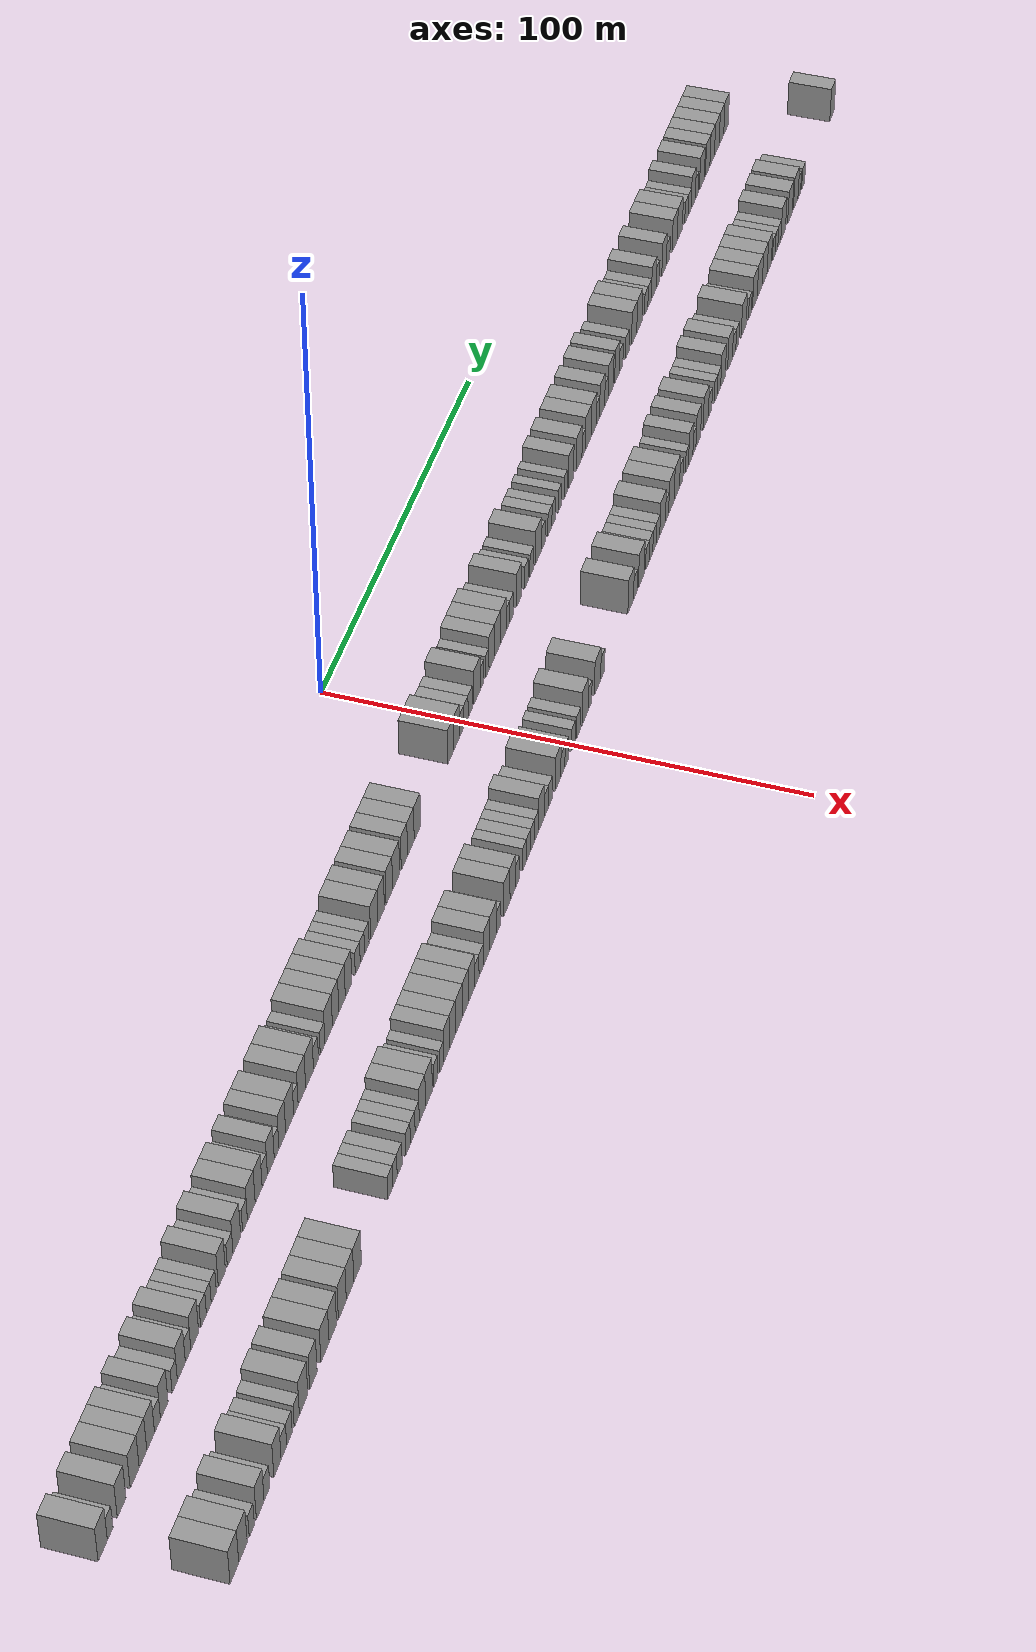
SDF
<sdf version="1.6">
 <world name="default">
  <scene>
   <sky><clouds><speed>12</speed></clouds></sky>
   <ambient>0.4 0.4 0.4 1</ambient>
   <background>0.7 0.7 0.7 1</background>
   <shadows>1</shadows>
  </scene>
  <gravity>0 0 -9.8066</gravity>
  <magnetic_field>6e-06 2.3e-05 -4.2e-05</magnetic_field>
  <physics default="0" name="default_physics" type="ode">
   <ode>
    <solver>
     <type>quick</type>
     <iters>10</iters>
     <sor>1.0</sor>
     <use_dynamic_moi_rescaling>0</use_dynamic_moi_rescaling>
    </solver>
    <constraints>
     <cfm>0</cfm>
     <erp>0.2</erp>
     <contact_max_correcting_vel>100</contact_max_correcting_vel>
     <contact_surface_layer>0.001</contact_surface_layer>
    </constraints>
   </ode>
   <max_step_size>0.004</max_step_size>
   <real_time_factor>1</real_time_factor>
   <real_time_update_rate>250</real_time_update_rate>
  </physics>
  <light name="sun" type="directional">
   <pose>0 0 10 0 0 0</pose>
   <diffuse>0.8 0.8 0.8 1</diffuse>
   <specular>0.2 0.2 0.2 1</specular>
   <attenuation>
    <range>1000</range>
    <constant>0.9</constant>
    <linear>0.01</linear>
    <quadratic>0.001</quadratic>
   </attenuation>
   <direction>-0.5 0.1 -0.9</direction>
  </light>
  <model name="building_1">
   <static>1</static>
   <pose>25.0000 -201.8537 0 0.000000 0.000000 0.000000</pose>
   <link name="link">
    <pose>0 0 4.50 0 0 0</pose>
    <collision name="collision"><geometry><box><size>10.0000 4.2926 9.0000</size></box></geometry></collision>
    <visual name="visual">
     <cast_shadows>0</cast_shadows>
     <geometry><box><size>10.0000 4.2926 9.0000</size></box></geometry>
     <material>
      <script>
       <uri>model://grey_wall/materials/scripts</uri>
       <uri>model://grey_wall/materials/textures</uri>
       <name>vrc/grey_wall</name>
      </script>
     </material>
    </visual>
   </link>
  </model>
  <model name="building_2">
   <static>1</static>
   <pose>25.0000 -198.4065 0 0.000000 0.000000 0.000000</pose>
   <link name="link">
    <pose>0 0 3.00 0 0 0</pose>
    <collision name="collision"><geometry><box><size>10.0000 2.6019 6.0000</size></box></geometry></collision>
    <visual name="visual">
     <cast_shadows>0</cast_shadows>
     <geometry><box><size>10.0000 2.6019 6.0000</size></box></geometry>
     <material>
      <script>
       <uri>model://grey_wall/materials/scripts</uri>
       <uri>model://grey_wall/materials/textures</uri>
       <name>vrc/grey_wall</name>
      </script>
     </material>
    </visual>
   </link>
  </model>
  <model name="building_3">
   <static>1</static>
   <pose>25.0000 -193.0528 0 0.000000 0.000000 0.000000</pose>
   <link name="link">
    <pose>0 0 4.50 0 0 0</pose>
    <collision name="collision"><geometry><box><size>10.0000 4.1055 9.0000</size></box></geometry></collision>
    <visual name="visual">
     <cast_shadows>0</cast_shadows>
     <geometry><box><size>10.0000 4.1055 9.0000</size></box></geometry>
     <material>
      <script>
       <uri>model://grey_wall/materials/scripts</uri>
       <uri>model://grey_wall/materials/textures</uri>
       <name>vrc/grey_wall</name>
      </script>
     </material>
    </visual>
   </link>
  </model>
  <model name="building_4">
   <static>1</static>
   <pose>25.0000 -186.8608 0 0.000000 0.000000 0.000000</pose>
   <link name="link">
    <pose>0 0 4.50 0 0 0</pose>
    <collision name="collision"><geometry><box><size>10.0000 4.2785 9.0000</size></box></geometry></collision>
    <visual name="visual">
     <cast_shadows>0</cast_shadows>
     <geometry><box><size>10.0000 4.2785 9.0000</size></box></geometry>
     <material>
      <script>
       <uri>model://grey_wall/materials/scripts</uri>
       <uri>model://grey_wall/materials/textures</uri>
       <name>vrc/grey_wall</name>
      </script>
     </material>
    </visual>
   </link>
  </model>
  <model name="building_5">
   <static>1</static>
   <pose>25.0000 -182.8801 0 0.000000 0.000000 0.000000</pose>
   <link name="link">
    <pose>0 0 4.50 0 0 0</pose>
    <collision name="collision"><geometry><box><size>10.0000 3.6829 9.0000</size></box></geometry></collision>
    <visual name="visual">
     <cast_shadows>0</cast_shadows>
     <geometry><box><size>10.0000 3.6829 9.0000</size></box></geometry>
     <material>
      <script>
       <uri>model://grey_wall/materials/scripts</uri>
       <uri>model://grey_wall/materials/textures</uri>
       <name>vrc/grey_wall</name>
      </script>
     </material>
    </visual>
   </link>
  </model>
  <model name="building_6">
   <static>1</static>
   <pose>25.0000 -179.1842 0 0.000000 0.000000 0.000000</pose>
   <link name="link">
    <pose>0 0 4.50 0 0 0</pose>
    <collision name="collision"><geometry><box><size>10.0000 3.7089 9.0000</size></box></geometry></collision>
    <visual name="visual">
     <cast_shadows>0</cast_shadows>
     <geometry><box><size>10.0000 3.7089 9.0000</size></box></geometry>
     <material>
      <script>
       <uri>model://grey_wall/materials/scripts</uri>
       <uri>model://grey_wall/materials/textures</uri>
       <name>vrc/grey_wall</name>
      </script>
     </material>
    </visual>
   </link>
  </model>
  <model name="building_7">
   <static>1</static>
   <pose>25.0000 -175.8771 0 0.000000 0.000000 0.000000</pose>
   <link name="link">
    <pose>0 0 3.00 0 0 0</pose>
    <collision name="collision"><geometry><box><size>10.0000 2.9053 6.0000</size></box></geometry></collision>
    <visual name="visual">
     <cast_shadows>0</cast_shadows>
     <geometry><box><size>10.0000 2.9053 6.0000</size></box></geometry>
     <material>
      <script>
       <uri>model://grey_wall/materials/scripts</uri>
       <uri>model://grey_wall/materials/textures</uri>
       <name>vrc/grey_wall</name>
      </script>
     </material>
    </visual>
   </link>
  </model>
  <model name="building_8">
   <static>1</static>
   <pose>25.0000 -172.5661 0 0.000000 0.000000 0.000000</pose>
   <link name="link">
    <pose>0 0 4.50 0 0 0</pose>
    <collision name="collision"><geometry><box><size>10.0000 3.7166 9.0000</size></box></geometry></collision>
    <visual name="visual">
     <cast_shadows>0</cast_shadows>
     <geometry><box><size>10.0000 3.7166 9.0000</size></box></geometry>
     <material>
      <script>
       <uri>model://grey_wall/materials/scripts</uri>
       <uri>model://grey_wall/materials/textures</uri>
       <name>vrc/grey_wall</name>
      </script>
     </material>
    </visual>
   </link>
  </model>
  <model name="building_9">
   <static>1</static>
   <pose>25.0000 -167.4153 0 0.000000 0.000000 0.000000</pose>
   <link name="link">
    <pose>0 0 3.00 0 0 0</pose>
    <collision name="collision"><geometry><box><size>10.0000 2.5850 6.0000</size></box></geometry></collision>
    <visual name="visual">
     <cast_shadows>0</cast_shadows>
     <geometry><box><size>10.0000 2.5850 6.0000</size></box></geometry>
     <material>
      <script>
       <uri>model://grey_wall/materials/scripts</uri>
       <uri>model://grey_wall/materials/textures</uri>
       <name>vrc/grey_wall</name>
      </script>
     </material>
    </visual>
   </link>
  </model>
  <model name="building_10">
   <static>1</static>
   <pose>25.0000 -164.1304 0 0.000000 0.000000 0.000000</pose>
   <link name="link">
    <pose>0 0 4.50 0 0 0</pose>
    <collision name="collision"><geometry><box><size>10.0000 3.9848 9.0000</size></box></geometry></collision>
    <visual name="visual">
     <cast_shadows>0</cast_shadows>
     <geometry><box><size>10.0000 3.9848 9.0000</size></box></geometry>
     <material>
      <script>
       <uri>model://grey_wall/materials/scripts</uri>
       <uri>model://grey_wall/materials/textures</uri>
       <name>vrc/grey_wall</name>
      </script>
     </material>
    </visual>
   </link>
  </model>
  <model name="building_11">
   <static>1</static>
   <pose>25.0000 -160.7675 0 0.000000 0.000000 0.000000</pose>
   <link name="link">
    <pose>0 0 3.00 0 0 0</pose>
    <collision name="collision"><geometry><box><size>10.0000 2.7411 6.0000</size></box></geometry></collision>
    <visual name="visual">
     <cast_shadows>0</cast_shadows>
     <geometry><box><size>10.0000 2.7411 6.0000</size></box></geometry>
     <material>
      <script>
       <uri>model://grey_wall/materials/scripts</uri>
       <uri>model://grey_wall/materials/textures</uri>
       <name>vrc/grey_wall</name>
      </script>
     </material>
    </visual>
   </link>
  </model>
  <model name="building_12">
   <static>1</static>
   <pose>25.0000 -157.4138 0 0.000000 0.000000 0.000000</pose>
   <link name="link">
    <pose>0 0 4.50 0 0 0</pose>
    <collision name="collision"><geometry><box><size>10.0000 3.9663 9.0000</size></box></geometry></collision>
    <visual name="visual">
     <cast_shadows>0</cast_shadows>
     <geometry><box><size>10.0000 3.9663 9.0000</size></box></geometry>
     <material>
      <script>
       <uri>model://grey_wall/materials/scripts</uri>
       <uri>model://grey_wall/materials/textures</uri>
       <name>vrc/grey_wall</name>
      </script>
     </material>
    </visual>
   </link>
  </model>
  <model name="building_13">
   <static>1</static>
   <pose>25.0000 -152.9617 0 0.000000 0.000000 0.000000</pose>
   <link name="link">
    <pose>0 0 3.00 0 0 0</pose>
    <collision name="collision"><geometry><box><size>10.0000 2.9379 6.0000</size></box></geometry></collision>
    <visual name="visual">
     <cast_shadows>0</cast_shadows>
     <geometry><box><size>10.0000 2.9379 6.0000</size></box></geometry>
     <material>
      <script>
       <uri>model://grey_wall/materials/scripts</uri>
       <uri>model://grey_wall/materials/textures</uri>
       <name>vrc/grey_wall</name>
      </script>
     </material>
    </visual>
   </link>
  </model>
  <model name="building_14">
   <static>1</static>
   <pose>25.0000 -150.2623 0 0.000000 0.000000 0.000000</pose>
   <link name="link">
    <pose>0 0 3.00 0 0 0</pose>
    <collision name="collision"><geometry><box><size>10.0000 2.4608 6.0000</size></box></geometry></collision>
    <visual name="visual">
     <cast_shadows>0</cast_shadows>
     <geometry><box><size>10.0000 2.4608 6.0000</size></box></geometry>
     <material>
      <script>
       <uri>model://grey_wall/materials/scripts</uri>
       <uri>model://grey_wall/materials/textures</uri>
       <name>vrc/grey_wall</name>
      </script>
     </material>
    </visual>
   </link>
  </model>
  <model name="building_15">
   <static>1</static>
   <pose>25.0000 -147.7212 0 0.000000 0.000000 0.000000</pose>
   <link name="link">
    <pose>0 0 3.00 0 0 0</pose>
    <collision name="collision"><geometry><box><size>10.0000 2.6214 6.0000</size></box></geometry></collision>
    <visual name="visual">
     <cast_shadows>0</cast_shadows>
     <geometry><box><size>10.0000 2.6214 6.0000</size></box></geometry>
     <material>
      <script>
       <uri>model://grey_wall/materials/scripts</uri>
       <uri>model://grey_wall/materials/textures</uri>
       <name>vrc/grey_wall</name>
      </script>
     </material>
    </visual>
   </link>
  </model>
  <model name="building_16">
   <static>1</static>
   <pose>25.0000 -143.5604 0 0.000000 0.000000 0.000000</pose>
   <link name="link">
    <pose>0 0 4.50 0 0 0</pose>
    <collision name="collision"><geometry><box><size>10.0000 3.7002 9.0000</size></box></geometry></collision>
    <visual name="visual">
     <cast_shadows>0</cast_shadows>
     <geometry><box><size>10.0000 3.7002 9.0000</size></box></geometry>
     <material>
      <script>
       <uri>model://grey_wall/materials/scripts</uri>
       <uri>model://grey_wall/materials/textures</uri>
       <name>vrc/grey_wall</name>
      </script>
     </material>
    </visual>
   </link>
  </model>
  <model name="building_17">
   <static>1</static>
   <pose>25.0000 -139.2249 0 0.000000 0.000000 0.000000</pose>
   <link name="link">
    <pose>0 0 3.00 0 0 0</pose>
    <collision name="collision"><geometry><box><size>10.0000 2.9709 6.0000</size></box></geometry></collision>
    <visual name="visual">
     <cast_shadows>0</cast_shadows>
     <geometry><box><size>10.0000 2.9709 6.0000</size></box></geometry>
     <material>
      <script>
       <uri>model://grey_wall/materials/scripts</uri>
       <uri>model://grey_wall/materials/textures</uri>
       <name>vrc/grey_wall</name>
      </script>
     </material>
    </visual>
   </link>
  </model>
  <model name="building_18">
   <static>1</static>
   <pose>25.0000 -135.7327 0 0.000000 0.000000 0.000000</pose>
   <link name="link">
    <pose>0 0 4.50 0 0 0</pose>
    <collision name="collision"><geometry><box><size>10.0000 4.0134 9.0000</size></box></geometry></collision>
    <visual name="visual">
     <cast_shadows>0</cast_shadows>
     <geometry><box><size>10.0000 4.0134 9.0000</size></box></geometry>
     <material>
      <script>
       <uri>model://grey_wall/materials/scripts</uri>
       <uri>model://grey_wall/materials/textures</uri>
       <name>vrc/grey_wall</name>
      </script>
     </material>
    </visual>
   </link>
  </model>
  <model name="building_19">
   <static>1</static>
   <pose>25.0000 -131.4297 0 0.000000 0.000000 0.000000</pose>
   <link name="link">
    <pose>0 0 3.00 0 0 0</pose>
    <collision name="collision"><geometry><box><size>10.0000 2.5926 6.0000</size></box></geometry></collision>
    <visual name="visual">
     <cast_shadows>0</cast_shadows>
     <geometry><box><size>10.0000 2.5926 6.0000</size></box></geometry>
     <material>
      <script>
       <uri>model://grey_wall/materials/scripts</uri>
       <uri>model://grey_wall/materials/textures</uri>
       <name>vrc/grey_wall</name>
      </script>
     </material>
    </visual>
   </link>
  </model>
  <model name="building_20">
   <static>1</static>
   <pose>25.0000 -128.0775 0 0.000000 0.000000 0.000000</pose>
   <link name="link">
    <pose>0 0 4.50 0 0 0</pose>
    <collision name="collision"><geometry><box><size>10.0000 4.1117 9.0000</size></box></geometry></collision>
    <visual name="visual">
     <cast_shadows>0</cast_shadows>
     <geometry><box><size>10.0000 4.1117 9.0000</size></box></geometry>
     <material>
      <script>
       <uri>model://grey_wall/materials/scripts</uri>
       <uri>model://grey_wall/materials/textures</uri>
       <name>vrc/grey_wall</name>
      </script>
     </material>
    </visual>
   </link>
  </model>
  <model name="building_21">
   <static>1</static>
   <pose>25.0000 -124.1487 0 0.000000 0.000000 0.000000</pose>
   <link name="link">
    <pose>0 0 4.50 0 0 0</pose>
    <collision name="collision"><geometry><box><size>10.0000 3.7458 9.0000</size></box></geometry></collision>
    <visual name="visual">
     <cast_shadows>0</cast_shadows>
     <geometry><box><size>10.0000 3.7458 9.0000</size></box></geometry>
     <material>
      <script>
       <uri>model://grey_wall/materials/scripts</uri>
       <uri>model://grey_wall/materials/textures</uri>
       <name>vrc/grey_wall</name>
      </script>
     </material>
    </visual>
   </link>
  </model>
  <model name="building_22">
   <static>1</static>
   <pose>25.0000 -120.8417 0 0.000000 0.000000 0.000000</pose>
   <link name="link">
    <pose>0 0 3.00 0 0 0</pose>
    <collision name="collision"><geometry><box><size>10.0000 2.8683 6.0000</size></box></geometry></collision>
    <visual name="visual">
     <cast_shadows>0</cast_shadows>
     <geometry><box><size>10.0000 2.8683 6.0000</size></box></geometry>
     <material>
      <script>
       <uri>model://grey_wall/materials/scripts</uri>
       <uri>model://grey_wall/materials/textures</uri>
       <name>vrc/grey_wall</name>
      </script>
     </material>
    </visual>
   </link>
  </model>
  <model name="building_23">
   <static>1</static>
   <pose>25.0000 -117.5402 0 0.000000 0.000000 0.000000</pose>
   <link name="link">
    <pose>0 0 4.50 0 0 0</pose>
    <collision name="collision"><geometry><box><size>10.0000 3.7347 9.0000</size></box></geometry></collision>
    <visual name="visual">
     <cast_shadows>0</cast_shadows>
     <geometry><box><size>10.0000 3.7347 9.0000</size></box></geometry>
     <material>
      <script>
       <uri>model://grey_wall/materials/scripts</uri>
       <uri>model://grey_wall/materials/textures</uri>
       <name>vrc/grey_wall</name>
      </script>
     </material>
    </visual>
   </link>
  </model>
  <model name="building_24">
   <static>1</static>
   <pose>25.0000 -114.3938 0 0.000000 0.000000 0.000000</pose>
   <link name="link">
    <pose>0 0 3.00 0 0 0</pose>
    <collision name="collision"><geometry><box><size>10.0000 2.5581 6.0000</size></box></geometry></collision>
    <visual name="visual">
     <cast_shadows>0</cast_shadows>
     <geometry><box><size>10.0000 2.5581 6.0000</size></box></geometry>
     <material>
      <script>
       <uri>model://grey_wall/materials/scripts</uri>
       <uri>model://grey_wall/materials/textures</uri>
       <name>vrc/grey_wall</name>
      </script>
     </material>
    </visual>
   </link>
  </model>
  <model name="building_25">
   <static>1</static>
   <pose>25.0000 -111.2595 0 0.000000 0.000000 0.000000</pose>
   <link name="link">
    <pose>0 0 4.50 0 0 0</pose>
    <collision name="collision"><geometry><box><size>10.0000 3.7104 9.0000</size></box></geometry></collision>
    <visual name="visual">
     <cast_shadows>0</cast_shadows>
     <geometry><box><size>10.0000 3.7104 9.0000</size></box></geometry>
     <material>
      <script>
       <uri>model://grey_wall/materials/scripts</uri>
       <uri>model://grey_wall/materials/textures</uri>
       <name>vrc/grey_wall</name>
      </script>
     </material>
    </visual>
   </link>
  </model>
  <model name="building_26">
   <static>1</static>
   <pose>25.0000 -107.1808 0 0.000000 0.000000 0.000000</pose>
   <link name="link">
    <pose>0 0 4.50 0 0 0</pose>
    <collision name="collision"><geometry><box><size>10.0000 4.4472 9.0000</size></box></geometry></collision>
    <visual name="visual">
     <cast_shadows>0</cast_shadows>
     <geometry><box><size>10.0000 4.4472 9.0000</size></box></geometry>
     <material>
      <script>
       <uri>model://grey_wall/materials/scripts</uri>
       <uri>model://grey_wall/materials/textures</uri>
       <name>vrc/grey_wall</name>
      </script>
     </material>
    </visual>
   </link>
  </model>
  <model name="building_27">
   <static>1</static>
   <pose>25.0000 -103.7387 0 0.000000 0.000000 0.000000</pose>
   <link name="link">
    <pose>0 0 3.00 0 0 0</pose>
    <collision name="collision"><geometry><box><size>10.0000 2.4370 6.0000</size></box></geometry></collision>
    <visual name="visual">
     <cast_shadows>0</cast_shadows>
     <geometry><box><size>10.0000 2.4370 6.0000</size></box></geometry>
     <material>
      <script>
       <uri>model://grey_wall/materials/scripts</uri>
       <uri>model://grey_wall/materials/textures</uri>
       <name>vrc/grey_wall</name>
      </script>
     </material>
    </visual>
   </link>
  </model>
  <model name="building_28">
   <static>1</static>
   <pose>25.0000 -100.4080 0 0.000000 0.000000 0.000000</pose>
   <link name="link">
    <pose>0 0 4.50 0 0 0</pose>
    <collision name="collision"><geometry><box><size>10.0000 4.2245 9.0000</size></box></geometry></collision>
    <visual name="visual">
     <cast_shadows>0</cast_shadows>
     <geometry><box><size>10.0000 4.2245 9.0000</size></box></geometry>
     <material>
      <script>
       <uri>model://grey_wall/materials/scripts</uri>
       <uri>model://grey_wall/materials/textures</uri>
       <name>vrc/grey_wall</name>
      </script>
     </material>
    </visual>
   </link>
  </model>
  <model name="building_29">
   <static>1</static>
   <pose>25.0000 -96.0797 0 0.000000 0.000000 0.000000</pose>
   <link name="link">
    <pose>0 0 4.50 0 0 0</pose>
    <collision name="collision"><geometry><box><size>10.0000 4.4322 9.0000</size></box></geometry></collision>
    <visual name="visual">
     <cast_shadows>0</cast_shadows>
     <geometry><box><size>10.0000 4.4322 9.0000</size></box></geometry>
     <material>
      <script>
       <uri>model://grey_wall/materials/scripts</uri>
       <uri>model://grey_wall/materials/textures</uri>
       <name>vrc/grey_wall</name>
      </script>
     </material>
    </visual>
   </link>
  </model>
  <model name="building_30">
   <static>1</static>
   <pose>25.0000 -92.4406 0 0.000000 0.000000 0.000000</pose>
   <link name="link">
    <pose>0 0 3.00 0 0 0</pose>
    <collision name="collision"><geometry><box><size>10.0000 2.8461 6.0000</size></box></geometry></collision>
    <visual name="visual">
     <cast_shadows>0</cast_shadows>
     <geometry><box><size>10.0000 2.8461 6.0000</size></box></geometry>
     <material>
      <script>
       <uri>model://grey_wall/materials/scripts</uri>
       <uri>model://grey_wall/materials/textures</uri>
       <name>vrc/grey_wall</name>
      </script>
     </material>
    </visual>
   </link>
  </model>
  <model name="building_31">
   <static>1</static>
   <pose>25.0000 -88.6851 0 0.000000 0.000000 0.000000</pose>
   <link name="link">
    <pose>0 0 3.00 0 0 0</pose>
    <collision name="collision"><geometry><box><size>10.0000 2.6649 6.0000</size></box></geometry></collision>
    <visual name="visual">
     <cast_shadows>0</cast_shadows>
     <geometry><box><size>10.0000 2.6649 6.0000</size></box></geometry>
     <material>
      <script>
       <uri>model://grey_wall/materials/scripts</uri>
       <uri>model://grey_wall/materials/textures</uri>
       <name>vrc/grey_wall</name>
      </script>
     </material>
    </visual>
   </link>
  </model>
  <model name="building_32">
   <static>1</static>
   <pose>25.0000 -85.1751 0 0.000000 0.000000 0.000000</pose>
   <link name="link">
    <pose>0 0 4.50 0 0 0</pose>
    <collision name="collision"><geometry><box><size>10.0000 4.3550 9.0000</size></box></geometry></collision>
    <visual name="visual">
     <cast_shadows>0</cast_shadows>
     <geometry><box><size>10.0000 4.3550 9.0000</size></box></geometry>
     <material>
      <script>
       <uri>model://grey_wall/materials/scripts</uri>
       <uri>model://grey_wall/materials/textures</uri>
       <name>vrc/grey_wall</name>
      </script>
     </material>
    </visual>
   </link>
  </model>
  <model name="building_33">
   <static>1</static>
   <pose>25.0000 -81.1255 0 0.000000 0.000000 0.000000</pose>
   <link name="link">
    <pose>0 0 4.50 0 0 0</pose>
    <collision name="collision"><geometry><box><size>10.0000 3.7442 9.0000</size></box></geometry></collision>
    <visual name="visual">
     <cast_shadows>0</cast_shadows>
     <geometry><box><size>10.0000 3.7442 9.0000</size></box></geometry>
     <material>
      <script>
       <uri>model://grey_wall/materials/scripts</uri>
       <uri>model://grey_wall/materials/textures</uri>
       <name>vrc/grey_wall</name>
      </script>
     </material>
    </visual>
   </link>
  </model>
  <model name="building_34">
   <static>1</static>
   <pose>25.0000 -77.3756 0 0.000000 0.000000 0.000000</pose>
   <link name="link">
    <pose>0 0 4.50 0 0 0</pose>
    <collision name="collision"><geometry><box><size>10.0000 3.7556 9.0000</size></box></geometry></collision>
    <visual name="visual">
     <cast_shadows>0</cast_shadows>
     <geometry><box><size>10.0000 3.7556 9.0000</size></box></geometry>
     <material>
      <script>
       <uri>model://grey_wall/materials/scripts</uri>
       <uri>model://grey_wall/materials/textures</uri>
       <name>vrc/grey_wall</name>
      </script>
     </material>
    </visual>
   </link>
  </model>
  <model name="building_35">
   <static>1</static>
   <pose>25.0000 -73.5626 0 0.000000 0.000000 0.000000</pose>
   <link name="link">
    <pose>0 0 4.50 0 0 0</pose>
    <collision name="collision"><geometry><box><size>10.0000 3.8703 9.0000</size></box></geometry></collision>
    <visual name="visual">
     <cast_shadows>0</cast_shadows>
     <geometry><box><size>10.0000 3.8703 9.0000</size></box></geometry>
     <material>
      <script>
       <uri>model://grey_wall/materials/scripts</uri>
       <uri>model://grey_wall/materials/textures</uri>
       <name>vrc/grey_wall</name>
      </script>
     </material>
    </visual>
   </link>
  </model>
  <model name="building_36">
   <static>1</static>
   <pose>25.0000 -68.1511 0 0.000000 0.000000 0.000000</pose>
   <link name="link">
    <pose>0 0 3.00 0 0 0</pose>
    <collision name="collision"><geometry><box><size>10.0000 2.9527 6.0000</size></box></geometry></collision>
    <visual name="visual">
     <cast_shadows>0</cast_shadows>
     <geometry><box><size>10.0000 2.9527 6.0000</size></box></geometry>
     <material>
      <script>
       <uri>model://grey_wall/materials/scripts</uri>
       <uri>model://grey_wall/materials/textures</uri>
       <name>vrc/grey_wall</name>
      </script>
     </material>
    </visual>
   </link>
  </model>
  <model name="building_37">
   <static>1</static>
   <pose>25.0000 -65.3780 0 0.000000 0.000000 0.000000</pose>
   <link name="link">
    <pose>0 0 3.00 0 0 0</pose>
    <collision name="collision"><geometry><box><size>10.0000 2.5935 6.0000</size></box></geometry></collision>
    <visual name="visual">
     <cast_shadows>0</cast_shadows>
     <geometry><box><size>10.0000 2.5935 6.0000</size></box></geometry>
     <material>
      <script>
       <uri>model://grey_wall/materials/scripts</uri>
       <uri>model://grey_wall/materials/textures</uri>
       <name>vrc/grey_wall</name>
      </script>
     </material>
    </visual>
   </link>
  </model>
  <model name="building_38">
   <static>1</static>
   <pose>25.0000 -62.7557 0 0.000000 0.000000 0.000000</pose>
   <link name="link">
    <pose>0 0 3.00 0 0 0</pose>
    <collision name="collision"><geometry><box><size>10.0000 2.6513 6.0000</size></box></geometry></collision>
    <visual name="visual">
     <cast_shadows>0</cast_shadows>
     <geometry><box><size>10.0000 2.6513 6.0000</size></box></geometry>
     <material>
      <script>
       <uri>model://grey_wall/materials/scripts</uri>
       <uri>model://grey_wall/materials/textures</uri>
       <name>vrc/grey_wall</name>
      </script>
     </material>
    </visual>
   </link>
  </model>
  <model name="building_39">
   <static>1</static>
   <pose>25.0000 -58.2150 0 0.000000 0.000000 0.000000</pose>
   <link name="link">
    <pose>0 0 4.50 0 0 0</pose>
    <collision name="collision"><geometry><box><size>10.0000 4.4300 9.0000</size></box></geometry></collision>
    <visual name="visual">
     <cast_shadows>0</cast_shadows>
     <geometry><box><size>10.0000 4.4300 9.0000</size></box></geometry>
     <material>
      <script>
       <uri>model://grey_wall/materials/scripts</uri>
       <uri>model://grey_wall/materials/textures</uri>
       <name>vrc/grey_wall</name>
      </script>
     </material>
    </visual>
   </link>
  </model>
  <model name="building_40">
   <static>1</static>
   <pose>25.0000 -54.0537 0 0.000000 0.000000 0.000000</pose>
   <link name="link">
    <pose>0 0 4.50 0 0 0</pose>
    <collision name="collision"><geometry><box><size>10.0000 3.8926 9.0000</size></box></geometry></collision>
    <visual name="visual">
     <cast_shadows>0</cast_shadows>
     <geometry><box><size>10.0000 3.8926 9.0000</size></box></geometry>
     <material>
      <script>
       <uri>model://grey_wall/materials/scripts</uri>
       <uri>model://grey_wall/materials/textures</uri>
       <name>vrc/grey_wall</name>
      </script>
     </material>
    </visual>
   </link>
  </model>
  <model name="building_41">
   <static>1</static>
   <pose>25.0000 -49.0728 0 0.000000 0.000000 0.000000</pose>
   <link name="link">
    <pose>0 0 4.50 0 0 0</pose>
    <collision name="collision"><geometry><box><size>10.0000 4.0693 9.0000</size></box></geometry></collision>
    <visual name="visual">
     <cast_shadows>0</cast_shadows>
     <geometry><box><size>10.0000 4.0693 9.0000</size></box></geometry>
     <material>
      <script>
       <uri>model://grey_wall/materials/scripts</uri>
       <uri>model://grey_wall/materials/textures</uri>
       <name>vrc/grey_wall</name>
      </script>
     </material>
    </visual>
   </link>
  </model>
  <model name="building_42">
   <static>1</static>
   <pose>25.0000 -44.8768 0 0.000000 0.000000 0.000000</pose>
   <link name="link">
    <pose>0 0 4.50 0 0 0</pose>
    <collision name="collision"><geometry><box><size>10.0000 4.3227 9.0000</size></box></geometry></collision>
    <visual name="visual">
     <cast_shadows>0</cast_shadows>
     <geometry><box><size>10.0000 4.3227 9.0000</size></box></geometry>
     <material>
      <script>
       <uri>model://grey_wall/materials/scripts</uri>
       <uri>model://grey_wall/materials/textures</uri>
       <name>vrc/grey_wall</name>
      </script>
     </material>
    </visual>
   </link>
  </model>
  <model name="building_43">
   <static>1</static>
   <pose>25.0000 -39.7487 0 0.000000 0.000000 0.000000</pose>
   <link name="link">
    <pose>0 0 4.50 0 0 0</pose>
    <collision name="collision"><geometry><box><size>10.0000 3.9335 9.0000</size></box></geometry></collision>
    <visual name="visual">
     <cast_shadows>0</cast_shadows>
     <geometry><box><size>10.0000 3.9335 9.0000</size></box></geometry>
     <material>
      <script>
       <uri>model://grey_wall/materials/scripts</uri>
       <uri>model://grey_wall/materials/textures</uri>
       <name>vrc/grey_wall</name>
      </script>
     </material>
    </visual>
   </link>
  </model>
  <model name="building_44">
   <static>1</static>
   <pose>25.0000 -35.6956 0 0.000000 0.000000 0.000000</pose>
   <link name="link">
    <pose>0 0 4.50 0 0 0</pose>
    <collision name="collision"><geometry><box><size>10.0000 4.1726 9.0000</size></box></geometry></collision>
    <visual name="visual">
     <cast_shadows>0</cast_shadows>
     <geometry><box><size>10.0000 4.1726 9.0000</size></box></geometry>
     <material>
      <script>
       <uri>model://grey_wall/materials/scripts</uri>
       <uri>model://grey_wall/materials/textures</uri>
       <name>vrc/grey_wall</name>
      </script>
     </material>
    </visual>
   </link>
  </model>
  <model name="building_45">
   <static>1</static>
   <pose>25.0000 -31.5699 0 0.000000 0.000000 0.000000</pose>
   <link name="link">
    <pose>0 0 4.50 0 0 0</pose>
    <collision name="collision"><geometry><box><size>10.0000 4.0788 9.0000</size></box></geometry></collision>
    <visual name="visual">
     <cast_shadows>0</cast_shadows>
     <geometry><box><size>10.0000 4.0788 9.0000</size></box></geometry>
     <material>
      <script>
       <uri>model://grey_wall/materials/scripts</uri>
       <uri>model://grey_wall/materials/textures</uri>
       <name>vrc/grey_wall</name>
      </script>
     </material>
    </visual>
   </link>
  </model>
  <model name="building_46">
   <static>1</static>
   <pose>25.0000 -10.1007 0 0.000000 0.000000 0.000000</pose>
   <link name="link">
    <pose>0 0 4.50 0 0 0</pose>
    <collision name="collision"><geometry><box><size>10.0000 3.6199 9.0000</size></box></geometry></collision>
    <visual name="visual">
     <cast_shadows>0</cast_shadows>
     <geometry><box><size>10.0000 3.6199 9.0000</size></box></geometry>
     <material>
      <script>
       <uri>model://grey_wall/materials/scripts</uri>
       <uri>model://grey_wall/materials/textures</uri>
       <name>vrc/grey_wall</name>
      </script>
     </material>
    </visual>
   </link>
  </model>
  <model name="building_47">
   <static>1</static>
   <pose>25.0000 -6.3358 0 0.000000 0.000000 0.000000</pose>
   <link name="link">
    <pose>0 0 4.50 0 0 0</pose>
    <collision name="collision"><geometry><box><size>10.0000 3.9100 9.0000</size></box></geometry></collision>
    <visual name="visual">
     <cast_shadows>0</cast_shadows>
     <geometry><box><size>10.0000 3.9100 9.0000</size></box></geometry>
     <material>
      <script>
       <uri>model://grey_wall/materials/scripts</uri>
       <uri>model://grey_wall/materials/textures</uri>
       <name>vrc/grey_wall</name>
      </script>
     </material>
    </visual>
   </link>
  </model>
  <model name="building_48">
   <static>1</static>
   <pose>25.0000 -2.8860 0 0.000000 0.000000 0.000000</pose>
   <link name="link">
    <pose>0 0 3.00 0 0 0</pose>
    <collision name="collision"><geometry><box><size>10.0000 2.9895 6.0000</size></box></geometry></collision>
    <visual name="visual">
     <cast_shadows>0</cast_shadows>
     <geometry><box><size>10.0000 2.9895 6.0000</size></box></geometry>
     <material>
      <script>
       <uri>model://grey_wall/materials/scripts</uri>
       <uri>model://grey_wall/materials/textures</uri>
       <name>vrc/grey_wall</name>
      </script>
     </material>
    </visual>
   </link>
  </model>
  <model name="building_49">
   <static>1</static>
   <pose>25.0000 0.0297 0 0.000000 0.000000 0.000000</pose>
   <link name="link">
    <pose>0 0 3.00 0 0 0</pose>
    <collision name="collision"><geometry><box><size>10.0000 2.8418 6.0000</size></box></geometry></collision>
    <visual name="visual">
     <cast_shadows>0</cast_shadows>
     <geometry><box><size>10.0000 2.8418 6.0000</size></box></geometry>
     <material>
      <script>
       <uri>model://grey_wall/materials/scripts</uri>
       <uri>model://grey_wall/materials/textures</uri>
       <name>vrc/grey_wall</name>
      </script>
     </material>
    </visual>
   </link>
  </model>
  <model name="building_50">
   <static>1</static>
   <pose>25.0000 2.9103 0 0.000000 0.000000 0.000000</pose>
   <link name="link">
    <pose>0 0 3.00 0 0 0</pose>
    <collision name="collision"><geometry><box><size>10.0000 2.9194 6.0000</size></box></geometry></collision>
    <visual name="visual">
     <cast_shadows>0</cast_shadows>
     <geometry><box><size>10.0000 2.9194 6.0000</size></box></geometry>
     <material>
      <script>
       <uri>model://grey_wall/materials/scripts</uri>
       <uri>model://grey_wall/materials/textures</uri>
       <name>vrc/grey_wall</name>
      </script>
     </material>
    </visual>
   </link>
  </model>
  <model name="building_51">
   <static>1</static>
   <pose>25.0000 7.5090 0 0.000000 0.000000 0.000000</pose>
   <link name="link">
    <pose>0 0 4.50 0 0 0</pose>
    <collision name="collision"><geometry><box><size>10.0000 4.2781 9.0000</size></box></geometry></collision>
    <visual name="visual">
     <cast_shadows>0</cast_shadows>
     <geometry><box><size>10.0000 4.2781 9.0000</size></box></geometry>
     <material>
      <script>
       <uri>model://grey_wall/materials/scripts</uri>
       <uri>model://grey_wall/materials/textures</uri>
       <name>vrc/grey_wall</name>
      </script>
     </material>
    </visual>
   </link>
  </model>
  <model name="building_52">
   <static>1</static>
   <pose>25.0000 10.8763 0 0.000000 0.000000 0.000000</pose>
   <link name="link">
    <pose>0 0 3.00 0 0 0</pose>
    <collision name="collision"><geometry><box><size>10.0000 2.4564 6.0000</size></box></geometry></collision>
    <visual name="visual">
     <cast_shadows>0</cast_shadows>
     <geometry><box><size>10.0000 2.4564 6.0000</size></box></geometry>
     <material>
      <script>
       <uri>model://grey_wall/materials/scripts</uri>
       <uri>model://grey_wall/materials/textures</uri>
       <name>vrc/grey_wall</name>
      </script>
     </material>
    </visual>
   </link>
  </model>
  <model name="building_53">
   <static>1</static>
   <pose>25.0000 14.3415 0 0.000000 0.000000 0.000000</pose>
   <link name="link">
    <pose>0 0 3.00 0 0 0</pose>
    <collision name="collision"><geometry><box><size>10.0000 2.4740 6.0000</size></box></geometry></collision>
    <visual name="visual">
     <cast_shadows>0</cast_shadows>
     <geometry><box><size>10.0000 2.4740 6.0000</size></box></geometry>
     <material>
      <script>
       <uri>model://grey_wall/materials/scripts</uri>
       <uri>model://grey_wall/materials/textures</uri>
       <name>vrc/grey_wall</name>
      </script>
     </material>
    </visual>
   </link>
  </model>
  <model name="building_54">
   <static>1</static>
   <pose>25.0000 17.4514 0 0.000000 0.000000 0.000000</pose>
   <link name="link">
    <pose>0 0 4.50 0 0 0</pose>
    <collision name="collision"><geometry><box><size>10.0000 3.7459 9.0000</size></box></geometry></collision>
    <visual name="visual">
     <cast_shadows>0</cast_shadows>
     <geometry><box><size>10.0000 3.7459 9.0000</size></box></geometry>
     <material>
      <script>
       <uri>model://grey_wall/materials/scripts</uri>
       <uri>model://grey_wall/materials/textures</uri>
       <name>vrc/grey_wall</name>
      </script>
     </material>
    </visual>
   </link>
  </model>
  <model name="building_55">
   <static>1</static>
   <pose>25.0000 21.4215 0 0.000000 0.000000 0.000000</pose>
   <link name="link">
    <pose>0 0 4.50 0 0 0</pose>
    <collision name="collision"><geometry><box><size>10.0000 4.1944 9.0000</size></box></geometry></collision>
    <visual name="visual">
     <cast_shadows>0</cast_shadows>
     <geometry><box><size>10.0000 4.1944 9.0000</size></box></geometry>
     <material>
      <script>
       <uri>model://grey_wall/materials/scripts</uri>
       <uri>model://grey_wall/materials/textures</uri>
       <name>vrc/grey_wall</name>
      </script>
     </material>
    </visual>
   </link>
  </model>
  <model name="building_56">
   <static>1</static>
   <pose>25.0000 25.5476 0 0.000000 0.000000 0.000000</pose>
   <link name="link">
    <pose>0 0 4.50 0 0 0</pose>
    <collision name="collision"><geometry><box><size>10.0000 4.0577 9.0000</size></box></geometry></collision>
    <visual name="visual">
     <cast_shadows>0</cast_shadows>
     <geometry><box><size>10.0000 4.0577 9.0000</size></box></geometry>
     <material>
      <script>
       <uri>model://grey_wall/materials/scripts</uri>
       <uri>model://grey_wall/materials/textures</uri>
       <name>vrc/grey_wall</name>
      </script>
     </material>
    </visual>
   </link>
  </model>
  <model name="building_57">
   <static>1</static>
   <pose>25.0000 28.7807 0 0.000000 0.000000 0.000000</pose>
   <link name="link">
    <pose>0 0 3.00 0 0 0</pose>
    <collision name="collision"><geometry><box><size>10.0000 2.4084 6.0000</size></box></geometry></collision>
    <visual name="visual">
     <cast_shadows>0</cast_shadows>
     <geometry><box><size>10.0000 2.4084 6.0000</size></box></geometry>
     <material>
      <script>
       <uri>model://grey_wall/materials/scripts</uri>
       <uri>model://grey_wall/materials/textures</uri>
       <name>vrc/grey_wall</name>
      </script>
     </material>
    </visual>
   </link>
  </model>
  <model name="building_58">
   <static>1</static>
   <pose>25.0000 31.3648 0 0.000000 0.000000 0.000000</pose>
   <link name="link">
    <pose>0 0 3.00 0 0 0</pose>
    <collision name="collision"><geometry><box><size>10.0000 2.7599 6.0000</size></box></geometry></collision>
    <visual name="visual">
     <cast_shadows>0</cast_shadows>
     <geometry><box><size>10.0000 2.7599 6.0000</size></box></geometry>
     <material>
      <script>
       <uri>model://grey_wall/materials/scripts</uri>
       <uri>model://grey_wall/materials/textures</uri>
       <name>vrc/grey_wall</name>
      </script>
     </material>
    </visual>
   </link>
  </model>
  <model name="building_59">
   <static>1</static>
   <pose>25.0000 36.6271 0 0.000000 0.000000 0.000000</pose>
   <link name="link">
    <pose>0 0 4.50 0 0 0</pose>
    <collision name="collision"><geometry><box><size>10.0000 3.7646 9.0000</size></box></geometry></collision>
    <visual name="visual">
     <cast_shadows>0</cast_shadows>
     <geometry><box><size>10.0000 3.7646 9.0000</size></box></geometry>
     <material>
      <script>
       <uri>model://grey_wall/materials/scripts</uri>
       <uri>model://grey_wall/materials/textures</uri>
       <name>vrc/grey_wall</name>
      </script>
     </material>
    </visual>
   </link>
  </model>
  <model name="building_60">
   <static>1</static>
   <pose>25.0000 41.8939 0 0.000000 0.000000 0.000000</pose>
   <link name="link">
    <pose>0 0 3.00 0 0 0</pose>
    <collision name="collision"><geometry><box><size>10.0000 2.7690 6.0000</size></box></geometry></collision>
    <visual name="visual">
     <cast_shadows>0</cast_shadows>
     <geometry><box><size>10.0000 2.7690 6.0000</size></box></geometry>
     <material>
      <script>
       <uri>model://grey_wall/materials/scripts</uri>
       <uri>model://grey_wall/materials/textures</uri>
       <name>vrc/grey_wall</name>
      </script>
     </material>
    </visual>
   </link>
  </model>
  <model name="building_61">
   <static>1</static>
   <pose>25.0000 45.6931 0 0.000000 0.000000 0.000000</pose>
   <link name="link">
    <pose>0 0 3.00 0 0 0</pose>
    <collision name="collision"><geometry><box><size>10.0000 2.8296 6.0000</size></box></geometry></collision>
    <visual name="visual">
     <cast_shadows>0</cast_shadows>
     <geometry><box><size>10.0000 2.8296 6.0000</size></box></geometry>
     <material>
      <script>
       <uri>model://grey_wall/materials/scripts</uri>
       <uri>model://grey_wall/materials/textures</uri>
       <name>vrc/grey_wall</name>
      </script>
     </material>
    </visual>
   </link>
  </model>
  <model name="building_62">
   <static>1</static>
   <pose>25.0000 50.3358 0 0.000000 0.000000 0.000000</pose>
   <link name="link">
    <pose>0 0 4.50 0 0 0</pose>
    <collision name="collision"><geometry><box><size>10.0000 4.4559 9.0000</size></box></geometry></collision>
    <visual name="visual">
     <cast_shadows>0</cast_shadows>
     <geometry><box><size>10.0000 4.4559 9.0000</size></box></geometry>
     <material>
      <script>
       <uri>model://grey_wall/materials/scripts</uri>
       <uri>model://grey_wall/materials/textures</uri>
       <name>vrc/grey_wall</name>
      </script>
     </material>
    </visual>
   </link>
  </model>
  <model name="building_63">
   <static>1</static>
   <pose>25.0000 53.9256 0 0.000000 0.000000 0.000000</pose>
   <link name="link">
    <pose>0 0 3.00 0 0 0</pose>
    <collision name="collision"><geometry><box><size>10.0000 2.7237 6.0000</size></box></geometry></collision>
    <visual name="visual">
     <cast_shadows>0</cast_shadows>
     <geometry><box><size>10.0000 2.7237 6.0000</size></box></geometry>
     <material>
      <script>
       <uri>model://grey_wall/materials/scripts</uri>
       <uri>model://grey_wall/materials/textures</uri>
       <name>vrc/grey_wall</name>
      </script>
     </material>
    </visual>
   </link>
  </model>
  <model name="building_64">
   <static>1</static>
   <pose>25.0000 58.7681 0 0.000000 0.000000 0.000000</pose>
   <link name="link">
    <pose>0 0 3.00 0 0 0</pose>
    <collision name="collision"><geometry><box><size>10.0000 2.9613 6.0000</size></box></geometry></collision>
    <visual name="visual">
     <cast_shadows>0</cast_shadows>
     <geometry><box><size>10.0000 2.9613 6.0000</size></box></geometry>
     <material>
      <script>
       <uri>model://grey_wall/materials/scripts</uri>
       <uri>model://grey_wall/materials/textures</uri>
       <name>vrc/grey_wall</name>
      </script>
     </material>
    </visual>
   </link>
  </model>
  <model name="building_65">
   <static>1</static>
   <pose>25.0000 61.5337 0 0.000000 0.000000 0.000000</pose>
   <link name="link">
    <pose>0 0 3.00 0 0 0</pose>
    <collision name="collision"><geometry><box><size>10.0000 2.5700 6.0000</size></box></geometry></collision>
    <visual name="visual">
     <cast_shadows>0</cast_shadows>
     <geometry><box><size>10.0000 2.5700 6.0000</size></box></geometry>
     <material>
      <script>
       <uri>model://grey_wall/materials/scripts</uri>
       <uri>model://grey_wall/materials/textures</uri>
       <name>vrc/grey_wall</name>
      </script>
     </material>
    </visual>
   </link>
  </model>
  <model name="building_66">
   <static>1</static>
   <pose>25.0000 66.0421 0 0.000000 0.000000 0.000000</pose>
   <link name="link">
    <pose>0 0 3.00 0 0 0</pose>
    <collision name="collision"><geometry><box><size>10.0000 2.4468 6.0000</size></box></geometry></collision>
    <visual name="visual">
     <cast_shadows>0</cast_shadows>
     <geometry><box><size>10.0000 2.4468 6.0000</size></box></geometry>
     <material>
      <script>
       <uri>model://grey_wall/materials/scripts</uri>
       <uri>model://grey_wall/materials/textures</uri>
       <name>vrc/grey_wall</name>
      </script>
     </material>
    </visual>
   </link>
  </model>
  <model name="building_67">
   <static>1</static>
   <pose>25.0000 70.4713 0 0.000000 0.000000 0.000000</pose>
   <link name="link">
    <pose>0 0 3.00 0 0 0</pose>
    <collision name="collision"><geometry><box><size>10.0000 2.4115 6.0000</size></box></geometry></collision>
    <visual name="visual">
     <cast_shadows>0</cast_shadows>
     <geometry><box><size>10.0000 2.4115 6.0000</size></box></geometry>
     <material>
      <script>
       <uri>model://grey_wall/materials/scripts</uri>
       <uri>model://grey_wall/materials/textures</uri>
       <name>vrc/grey_wall</name>
      </script>
     </material>
    </visual>
   </link>
  </model>
  <model name="building_68">
   <static>1</static>
   <pose>25.0000 74.5765 0 0.000000 0.000000 0.000000</pose>
   <link name="link">
    <pose>0 0 4.50 0 0 0</pose>
    <collision name="collision"><geometry><box><size>10.0000 3.7988 9.0000</size></box></geometry></collision>
    <visual name="visual">
     <cast_shadows>0</cast_shadows>
     <geometry><box><size>10.0000 3.7988 9.0000</size></box></geometry>
     <material>
      <script>
       <uri>model://grey_wall/materials/scripts</uri>
       <uri>model://grey_wall/materials/textures</uri>
       <name>vrc/grey_wall</name>
      </script>
     </material>
    </visual>
   </link>
  </model>
  <model name="building_69">
   <static>1</static>
   <pose>25.0000 80.6186 0 0.000000 0.000000 0.000000</pose>
   <link name="link">
    <pose>0 0 4.50 0 0 0</pose>
    <collision name="collision"><geometry><box><size>10.0000 4.2855 9.0000</size></box></geometry></collision>
    <visual name="visual">
     <cast_shadows>0</cast_shadows>
     <geometry><box><size>10.0000 4.2855 9.0000</size></box></geometry>
     <material>
      <script>
       <uri>model://grey_wall/materials/scripts</uri>
       <uri>model://grey_wall/materials/textures</uri>
       <name>vrc/grey_wall</name>
      </script>
     </material>
    </visual>
   </link>
  </model>
  <model name="building_70">
   <static>1</static>
   <pose>25.0000 84.1155 0 0.000000 0.000000 0.000000</pose>
   <link name="link">
    <pose>0 0 3.00 0 0 0</pose>
    <collision name="collision"><geometry><box><size>10.0000 2.7082 6.0000</size></box></geometry></collision>
    <visual name="visual">
     <cast_shadows>0</cast_shadows>
     <geometry><box><size>10.0000 2.7082 6.0000</size></box></geometry>
     <material>
      <script>
       <uri>model://grey_wall/materials/scripts</uri>
       <uri>model://grey_wall/materials/textures</uri>
       <name>vrc/grey_wall</name>
      </script>
     </material>
    </visual>
   </link>
  </model>
  <model name="building_71">
   <static>1</static>
   <pose>25.0000 87.6182 0 0.000000 0.000000 0.000000</pose>
   <link name="link">
    <pose>0 0 4.50 0 0 0</pose>
    <collision name="collision"><geometry><box><size>10.0000 4.2970 9.0000</size></box></geometry></collision>
    <visual name="visual">
     <cast_shadows>0</cast_shadows>
     <geometry><box><size>10.0000 4.2970 9.0000</size></box></geometry>
     <material>
      <script>
       <uri>model://grey_wall/materials/scripts</uri>
       <uri>model://grey_wall/materials/textures</uri>
       <name>vrc/grey_wall</name>
      </script>
     </material>
    </visual>
   </link>
  </model>
  <model name="building_72">
   <static>1</static>
   <pose>25.0000 91.8586 0 0.000000 0.000000 0.000000</pose>
   <link name="link">
    <pose>0 0 4.50 0 0 0</pose>
    <collision name="collision"><geometry><box><size>10.0000 4.1838 9.0000</size></box></geometry></collision>
    <visual name="visual">
     <cast_shadows>0</cast_shadows>
     <geometry><box><size>10.0000 4.1838 9.0000</size></box></geometry>
     <material>
      <script>
       <uri>model://grey_wall/materials/scripts</uri>
       <uri>model://grey_wall/materials/textures</uri>
       <name>vrc/grey_wall</name>
      </script>
     </material>
    </visual>
   </link>
  </model>
  <model name="building_73">
   <static>1</static>
   <pose>25.0000 95.1588 0 0.000000 0.000000 0.000000</pose>
   <link name="link">
    <pose>0 0 3.00 0 0 0</pose>
    <collision name="collision"><geometry><box><size>10.0000 2.4167 6.0000</size></box></geometry></collision>
    <visual name="visual">
     <cast_shadows>0</cast_shadows>
     <geometry><box><size>10.0000 2.4167 6.0000</size></box></geometry>
     <material>
      <script>
       <uri>model://grey_wall/materials/scripts</uri>
       <uri>model://grey_wall/materials/textures</uri>
       <name>vrc/grey_wall</name>
      </script>
     </material>
    </visual>
   </link>
  </model>
  <model name="building_74">
   <static>1</static>
   <pose>25.0000 98.3634 0 0.000000 0.000000 0.000000</pose>
   <link name="link">
    <pose>0 0 4.50 0 0 0</pose>
    <collision name="collision"><geometry><box><size>10.0000 3.9925 9.0000</size></box></geometry></collision>
    <visual name="visual">
     <cast_shadows>0</cast_shadows>
     <geometry><box><size>10.0000 3.9925 9.0000</size></box></geometry>
     <material>
      <script>
       <uri>model://grey_wall/materials/scripts</uri>
       <uri>model://grey_wall/materials/textures</uri>
       <name>vrc/grey_wall</name>
      </script>
     </material>
    </visual>
   </link>
  </model>
  <model name="building_75">
   <static>1</static>
   <pose>25.0000 101.7082 0 0.000000 0.000000 0.000000</pose>
   <link name="link">
    <pose>0 0 3.00 0 0 0</pose>
    <collision name="collision"><geometry><box><size>10.0000 2.6971 6.0000</size></box></geometry></collision>
    <visual name="visual">
     <cast_shadows>0</cast_shadows>
     <geometry><box><size>10.0000 2.6971 6.0000</size></box></geometry>
     <material>
      <script>
       <uri>model://grey_wall/materials/scripts</uri>
       <uri>model://grey_wall/materials/textures</uri>
       <name>vrc/grey_wall</name>
      </script>
     </material>
    </visual>
   </link>
  </model>
  <model name="building_76">
   <static>1</static>
   <pose>25.0000 105.1471 0 0.000000 0.000000 0.000000</pose>
   <link name="link">
    <pose>0 0 4.50 0 0 0</pose>
    <collision name="collision"><geometry><box><size>10.0000 4.1807 9.0000</size></box></geometry></collision>
    <visual name="visual">
     <cast_shadows>0</cast_shadows>
     <geometry><box><size>10.0000 4.1807 9.0000</size></box></geometry>
     <material>
      <script>
       <uri>model://grey_wall/materials/scripts</uri>
       <uri>model://grey_wall/materials/textures</uri>
       <name>vrc/grey_wall</name>
      </script>
     </material>
    </visual>
   </link>
  </model>
  <model name="building_77">
   <static>1</static>
   <pose>25.0000 110.0863 0 0.000000 0.000000 0.000000</pose>
   <link name="link">
    <pose>0 0 4.50 0 0 0</pose>
    <collision name="collision"><geometry><box><size>10.0000 3.6975 9.0000</size></box></geometry></collision>
    <visual name="visual">
     <cast_shadows>0</cast_shadows>
     <geometry><box><size>10.0000 3.6975 9.0000</size></box></geometry>
     <material>
      <script>
       <uri>model://grey_wall/materials/scripts</uri>
       <uri>model://grey_wall/materials/textures</uri>
       <name>vrc/grey_wall</name>
      </script>
     </material>
    </visual>
   </link>
  </model>
  <model name="building_78">
   <static>1</static>
   <pose>25.0000 113.3490 0 0.000000 0.000000 0.000000</pose>
   <link name="link">
    <pose>0 0 3.00 0 0 0</pose>
    <collision name="collision"><geometry><box><size>10.0000 2.8279 6.0000</size></box></geometry></collision>
    <visual name="visual">
     <cast_shadows>0</cast_shadows>
     <geometry><box><size>10.0000 2.8279 6.0000</size></box></geometry>
     <material>
      <script>
       <uri>model://grey_wall/materials/scripts</uri>
       <uri>model://grey_wall/materials/textures</uri>
       <name>vrc/grey_wall</name>
      </script>
     </material>
    </visual>
   </link>
  </model>
  <model name="building_79">
   <static>1</static>
   <pose>25.0000 118.2401 0 0.000000 0.000000 0.000000</pose>
   <link name="link">
    <pose>0 0 3.00 0 0 0</pose>
    <collision name="collision"><geometry><box><size>10.0000 2.9542 6.0000</size></box></geometry></collision>
    <visual name="visual">
     <cast_shadows>0</cast_shadows>
     <geometry><box><size>10.0000 2.9542 6.0000</size></box></geometry>
     <material>
      <script>
       <uri>model://grey_wall/materials/scripts</uri>
       <uri>model://grey_wall/materials/textures</uri>
       <name>vrc/grey_wall</name>
      </script>
     </material>
    </visual>
   </link>
  </model>
  <model name="building_80">
   <static>1</static>
   <pose>25.0000 123.8369 0 0.000000 0.000000 0.000000</pose>
   <link name="link">
    <pose>0 0 4.50 0 0 0</pose>
    <collision name="collision"><geometry><box><size>10.0000 4.2394 9.0000</size></box></geometry></collision>
    <visual name="visual">
     <cast_shadows>0</cast_shadows>
     <geometry><box><size>10.0000 4.2394 9.0000</size></box></geometry>
     <material>
      <script>
       <uri>model://grey_wall/materials/scripts</uri>
       <uri>model://grey_wall/materials/textures</uri>
       <name>vrc/grey_wall</name>
      </script>
     </material>
    </visual>
   </link>
  </model>
  <model name="building_81">
   <static>1</static>
   <pose>25.0000 128.1379 0 0.000000 0.000000 0.000000</pose>
   <link name="link">
    <pose>0 0 4.50 0 0 0</pose>
    <collision name="collision"><geometry><box><size>10.0000 4.3627 9.0000</size></box></geometry></collision>
    <visual name="visual">
     <cast_shadows>0</cast_shadows>
     <geometry><box><size>10.0000 4.3627 9.0000</size></box></geometry>
     <material>
      <script>
       <uri>model://grey_wall/materials/scripts</uri>
       <uri>model://grey_wall/materials/textures</uri>
       <name>vrc/grey_wall</name>
      </script>
     </material>
    </visual>
   </link>
  </model>
  <model name="building_82">
   <static>1</static>
   <pose>25.0000 133.6990 0 0.000000 0.000000 0.000000</pose>
   <link name="link">
    <pose>0 0 3.00 0 0 0</pose>
    <collision name="collision"><geometry><box><size>10.0000 2.7595 6.0000</size></box></geometry></collision>
    <visual name="visual">
     <cast_shadows>0</cast_shadows>
     <geometry><box><size>10.0000 2.7595 6.0000</size></box></geometry>
     <material>
      <script>
       <uri>model://grey_wall/materials/scripts</uri>
       <uri>model://grey_wall/materials/textures</uri>
       <name>vrc/grey_wall</name>
      </script>
     </material>
    </visual>
   </link>
  </model>
  <model name="building_83">
   <static>1</static>
   <pose>25.0000 136.5353 0 0.000000 0.000000 0.000000</pose>
   <link name="link">
    <pose>0 0 3.00 0 0 0</pose>
    <collision name="collision"><geometry><box><size>10.0000 2.9131 6.0000</size></box></geometry></collision>
    <visual name="visual">
     <cast_shadows>0</cast_shadows>
     <geometry><box><size>10.0000 2.9131 6.0000</size></box></geometry>
     <material>
      <script>
       <uri>model://grey_wall/materials/scripts</uri>
       <uri>model://grey_wall/materials/textures</uri>
       <name>vrc/grey_wall</name>
      </script>
     </material>
    </visual>
   </link>
  </model>
  <model name="building_84">
   <static>1</static>
   <pose>25.0000 139.9664 0 0.000000 0.000000 0.000000</pose>
   <link name="link">
    <pose>0 0 4.50 0 0 0</pose>
    <collision name="collision"><geometry><box><size>10.0000 3.9490 9.0000</size></box></geometry></collision>
    <visual name="visual">
     <cast_shadows>0</cast_shadows>
     <geometry><box><size>10.0000 3.9490 9.0000</size></box></geometry>
     <material>
      <script>
       <uri>model://grey_wall/materials/scripts</uri>
       <uri>model://grey_wall/materials/textures</uri>
       <name>vrc/grey_wall</name>
      </script>
     </material>
    </visual>
   </link>
  </model>
  <model name="building_85">
   <static>1</static>
   <pose>25.0000 143.3175 0 0.000000 0.000000 0.000000</pose>
   <link name="link">
    <pose>0 0 3.00 0 0 0</pose>
    <collision name="collision"><geometry><box><size>10.0000 2.7533 6.0000</size></box></geometry></collision>
    <visual name="visual">
     <cast_shadows>0</cast_shadows>
     <geometry><box><size>10.0000 2.7533 6.0000</size></box></geometry>
     <material>
      <script>
       <uri>model://grey_wall/materials/scripts</uri>
       <uri>model://grey_wall/materials/textures</uri>
       <name>vrc/grey_wall</name>
      </script>
     </material>
    </visual>
   </link>
  </model>
  <model name="building_86">
   <static>1</static>
   <pose>25.0000 148.6133 0 0.000000 0.000000 0.000000</pose>
   <link name="link">
    <pose>0 0 4.50 0 0 0</pose>
    <collision name="collision"><geometry><box><size>10.0000 3.8383 9.0000</size></box></geometry></collision>
    <visual name="visual">
     <cast_shadows>0</cast_shadows>
     <geometry><box><size>10.0000 3.8383 9.0000</size></box></geometry>
     <material>
      <script>
       <uri>model://grey_wall/materials/scripts</uri>
       <uri>model://grey_wall/materials/textures</uri>
       <name>vrc/grey_wall</name>
      </script>
     </material>
    </visual>
   </link>
  </model>
  <model name="building_87">
   <static>1</static>
   <pose>25.0000 151.9871 0 0.000000 0.000000 0.000000</pose>
   <link name="link">
    <pose>0 0 3.00 0 0 0</pose>
    <collision name="collision"><geometry><box><size>10.0000 2.9091 6.0000</size></box></geometry></collision>
    <visual name="visual">
     <cast_shadows>0</cast_shadows>
     <geometry><box><size>10.0000 2.9091 6.0000</size></box></geometry>
     <material>
      <script>
       <uri>model://grey_wall/materials/scripts</uri>
       <uri>model://grey_wall/materials/textures</uri>
       <name>vrc/grey_wall</name>
      </script>
     </material>
    </visual>
   </link>
  </model>
  <model name="building_88">
   <static>1</static>
   <pose>25.0000 157.6048 0 0.000000 0.000000 0.000000</pose>
   <link name="link">
    <pose>0 0 4.50 0 0 0</pose>
    <collision name="collision"><geometry><box><size>10.0000 4.3264 9.0000</size></box></geometry></collision>
    <visual name="visual">
     <cast_shadows>0</cast_shadows>
     <geometry><box><size>10.0000 4.3264 9.0000</size></box></geometry>
     <material>
      <script>
       <uri>model://grey_wall/materials/scripts</uri>
       <uri>model://grey_wall/materials/textures</uri>
       <name>vrc/grey_wall</name>
      </script>
     </material>
    </visual>
   </link>
  </model>
  <model name="building_89">
   <static>1</static>
   <pose>25.0000 162.0022 0 0.000000 0.000000 0.000000</pose>
   <link name="link">
    <pose>0 0 4.50 0 0 0</pose>
    <collision name="collision"><geometry><box><size>10.0000 4.4683 9.0000</size></box></geometry></collision>
    <visual name="visual">
     <cast_shadows>0</cast_shadows>
     <geometry><box><size>10.0000 4.4683 9.0000</size></box></geometry>
     <material>
      <script>
       <uri>model://grey_wall/materials/scripts</uri>
       <uri>model://grey_wall/materials/textures</uri>
       <name>vrc/grey_wall</name>
      </script>
     </material>
    </visual>
   </link>
  </model>
  <model name="building_90">
   <static>1</static>
   <pose>25.0000 167.7228 0 0.000000 0.000000 0.000000</pose>
   <link name="link">
    <pose>0 0 3.00 0 0 0</pose>
    <collision name="collision"><geometry><box><size>10.0000 2.9728 6.0000</size></box></geometry></collision>
    <visual name="visual">
     <cast_shadows>0</cast_shadows>
     <geometry><box><size>10.0000 2.9728 6.0000</size></box></geometry>
     <material>
      <script>
       <uri>model://grey_wall/materials/scripts</uri>
       <uri>model://grey_wall/materials/textures</uri>
       <name>vrc/grey_wall</name>
      </script>
     </material>
    </visual>
   </link>
  </model>
  <model name="building_91">
   <static>1</static>
   <pose>25.0000 170.4842 0 0.000000 0.000000 0.000000</pose>
   <link name="link">
    <pose>0 0 3.00 0 0 0</pose>
    <collision name="collision"><geometry><box><size>10.0000 2.5502 6.0000</size></box></geometry></collision>
    <visual name="visual">
     <cast_shadows>0</cast_shadows>
     <geometry><box><size>10.0000 2.5502 6.0000</size></box></geometry>
     <material>
      <script>
       <uri>model://grey_wall/materials/scripts</uri>
       <uri>model://grey_wall/materials/textures</uri>
       <name>vrc/grey_wall</name>
      </script>
     </material>
    </visual>
   </link>
  </model>
  <model name="building_92">
   <static>1</static>
   <pose>25.0000 173.5657 0 0.000000 0.000000 0.000000</pose>
   <link name="link">
    <pose>0 0 4.50 0 0 0</pose>
    <collision name="collision"><geometry><box><size>10.0000 3.6128 9.0000</size></box></geometry></collision>
    <visual name="visual">
     <cast_shadows>0</cast_shadows>
     <geometry><box><size>10.0000 3.6128 9.0000</size></box></geometry>
     <material>
      <script>
       <uri>model://grey_wall/materials/scripts</uri>
       <uri>model://grey_wall/materials/textures</uri>
       <name>vrc/grey_wall</name>
      </script>
     </material>
    </visual>
   </link>
  </model>
  <model name="building_93">
   <static>1</static>
   <pose>25.0000 176.7097 0 0.000000 0.000000 0.000000</pose>
   <link name="link">
    <pose>0 0 3.00 0 0 0</pose>
    <collision name="collision"><geometry><box><size>10.0000 2.6752 6.0000</size></box></geometry></collision>
    <visual name="visual">
     <cast_shadows>0</cast_shadows>
     <geometry><box><size>10.0000 2.6752 6.0000</size></box></geometry>
     <material>
      <script>
       <uri>model://grey_wall/materials/scripts</uri>
       <uri>model://grey_wall/materials/textures</uri>
       <name>vrc/grey_wall</name>
      </script>
     </material>
    </visual>
   </link>
  </model>
  <model name="building_94">
   <static>1</static>
   <pose>25.0000 181.1969 0 0.000000 0.000000 0.000000</pose>
   <link name="link">
    <pose>0 0 4.50 0 0 0</pose>
    <collision name="collision"><geometry><box><size>10.0000 4.2992 9.0000</size></box></geometry></collision>
    <visual name="visual">
     <cast_shadows>0</cast_shadows>
     <geometry><box><size>10.0000 4.2992 9.0000</size></box></geometry>
     <material>
      <script>
       <uri>model://grey_wall/materials/scripts</uri>
       <uri>model://grey_wall/materials/textures</uri>
       <name>vrc/grey_wall</name>
      </script>
     </material>
    </visual>
   </link>
  </model>
  <model name="building_95">
   <static>1</static>
   <pose>25.0000 186.3532 0 0.000000 0.000000 0.000000</pose>
   <link name="link">
    <pose>0 0 4.50 0 0 0</pose>
    <collision name="collision"><geometry><box><size>10.0000 4.0134 9.0000</size></box></geometry></collision>
    <visual name="visual">
     <cast_shadows>0</cast_shadows>
     <geometry><box><size>10.0000 4.0134 9.0000</size></box></geometry>
     <material>
      <script>
       <uri>model://grey_wall/materials/scripts</uri>
       <uri>model://grey_wall/materials/textures</uri>
       <name>vrc/grey_wall</name>
      </script>
     </material>
    </visual>
   </link>
  </model>
  <model name="building_96">
   <static>1</static>
   <pose>25.0000 190.3770 0 0.000000 0.000000 0.000000</pose>
   <link name="link">
    <pose>0 0 4.50 0 0 0</pose>
    <collision name="collision"><geometry><box><size>10.0000 4.0343 9.0000</size></box></geometry></collision>
    <visual name="visual">
     <cast_shadows>0</cast_shadows>
     <geometry><box><size>10.0000 4.0343 9.0000</size></box></geometry>
     <material>
      <script>
       <uri>model://grey_wall/materials/scripts</uri>
       <uri>model://grey_wall/materials/textures</uri>
       <name>vrc/grey_wall</name>
      </script>
     </material>
    </visual>
   </link>
  </model>
  <model name="building_97">
   <static>1</static>
   <pose>25.0000 194.5191 0 0.000000 0.000000 0.000000</pose>
   <link name="link">
    <pose>0 0 4.50 0 0 0</pose>
    <collision name="collision"><geometry><box><size>10.0000 4.2497 9.0000</size></box></geometry></collision>
    <visual name="visual">
     <cast_shadows>0</cast_shadows>
     <geometry><box><size>10.0000 4.2497 9.0000</size></box></geometry>
     <material>
      <script>
       <uri>model://grey_wall/materials/scripts</uri>
       <uri>model://grey_wall/materials/textures</uri>
       <name>vrc/grey_wall</name>
      </script>
     </material>
    </visual>
   </link>
  </model>
  <model name="building_98">
   <static>1</static>
   <pose>25.0000 198.7316 0 0.000000 0.000000 0.000000</pose>
   <link name="link">
    <pose>0 0 4.50 0 0 0</pose>
    <collision name="collision"><geometry><box><size>10.0000 4.1753 9.0000</size></box></geometry></collision>
    <visual name="visual">
     <cast_shadows>0</cast_shadows>
     <geometry><box><size>10.0000 4.1753 9.0000</size></box></geometry>
     <material>
      <script>
       <uri>model://grey_wall/materials/scripts</uri>
       <uri>model://grey_wall/materials/textures</uri>
       <name>vrc/grey_wall</name>
      </script>
     </material>
    </visual>
   </link>
  </model>
  <model name="building_99">
   <static>1</static>
   <pose>25.0000 202.8824 0 0.000000 0.000000 0.000000</pose>
   <link name="link">
    <pose>0 0 4.50 0 0 0</pose>
    <collision name="collision"><geometry><box><size>10.0000 4.1264 9.0000</size></box></geometry></collision>
    <visual name="visual">
     <cast_shadows>0</cast_shadows>
     <geometry><box><size>10.0000 4.1264 9.0000</size></box></geometry>
     <material>
      <script>
       <uri>model://grey_wall/materials/scripts</uri>
       <uri>model://grey_wall/materials/textures</uri>
       <name>vrc/grey_wall</name>
      </script>
     </material>
    </visual>
   </link>
  </model>
  <model name="building_100">
   <static>1</static>
   <pose>47.0000 -199.8662 0 0.000000 0.000000 0.000000</pose>
   <link name="link">
    <pose>0 0 4.50 0 0 0</pose>
    <collision name="collision"><geometry><box><size>10.0000 4.2677 9.0000</size></box></geometry></collision>
    <visual name="visual">
     <cast_shadows>0</cast_shadows>
     <geometry><box><size>10.0000 4.2677 9.0000</size></box></geometry>
     <material>
      <script>
       <uri>model://grey_wall/materials/scripts</uri>
       <uri>model://grey_wall/materials/textures</uri>
       <name>vrc/grey_wall</name>
      </script>
     </material>
    </visual>
   </link>
  </model>
  <model name="building_101">
   <static>1</static>
   <pose>47.0000 -195.6428 0 0.000000 0.000000 0.000000</pose>
   <link name="link">
    <pose>0 0 4.50 0 0 0</pose>
    <collision name="collision"><geometry><box><size>10.0000 4.1791 9.0000</size></box></geometry></collision>
    <visual name="visual">
     <cast_shadows>0</cast_shadows>
     <geometry><box><size>10.0000 4.1791 9.0000</size></box></geometry>
     <material>
      <script>
       <uri>model://grey_wall/materials/scripts</uri>
       <uri>model://grey_wall/materials/textures</uri>
       <name>vrc/grey_wall</name>
      </script>
     </material>
    </visual>
   </link>
  </model>
  <model name="building_102">
   <static>1</static>
   <pose>47.0000 -191.2650 0 0.000000 0.000000 0.000000</pose>
   <link name="link">
    <pose>0 0 3.00 0 0 0</pose>
    <collision name="collision"><geometry><box><size>10.0000 2.5765 6.0000</size></box></geometry></collision>
    <visual name="visual">
     <cast_shadows>0</cast_shadows>
     <geometry><box><size>10.0000 2.5765 6.0000</size></box></geometry>
     <material>
      <script>
       <uri>model://grey_wall/materials/scripts</uri>
       <uri>model://grey_wall/materials/textures</uri>
       <name>vrc/grey_wall</name>
      </script>
     </material>
    </visual>
   </link>
  </model>
  <model name="building_103">
   <static>1</static>
   <pose>47.0000 -187.0367 0 0.000000 0.000000 0.000000</pose>
   <link name="link">
    <pose>0 0 4.50 0 0 0</pose>
    <collision name="collision"><geometry><box><size>10.0000 3.8802 9.0000</size></box></geometry></collision>
    <visual name="visual">
     <cast_shadows>0</cast_shadows>
     <geometry><box><size>10.0000 3.8802 9.0000</size></box></geometry>
     <material>
      <script>
       <uri>model://grey_wall/materials/scripts</uri>
       <uri>model://grey_wall/materials/textures</uri>
       <name>vrc/grey_wall</name>
      </script>
     </material>
    </visual>
   </link>
  </model>
  <model name="building_104">
   <static>1</static>
   <pose>47.0000 -183.6220 0 0.000000 0.000000 0.000000</pose>
   <link name="link">
    <pose>0 0 3.00 0 0 0</pose>
    <collision name="collision"><geometry><box><size>10.0000 2.9492 6.0000</size></box></geometry></collision>
    <visual name="visual">
     <cast_shadows>0</cast_shadows>
     <geometry><box><size>10.0000 2.9492 6.0000</size></box></geometry>
     <material>
      <script>
       <uri>model://grey_wall/materials/scripts</uri>
       <uri>model://grey_wall/materials/textures</uri>
       <name>vrc/grey_wall</name>
      </script>
     </material>
    </visual>
   </link>
  </model>
  <model name="building_105">
   <static>1</static>
   <pose>47.0000 -178.2881 0 0.000000 0.000000 0.000000</pose>
   <link name="link">
    <pose>0 0 4.50 0 0 0</pose>
    <collision name="collision"><geometry><box><size>10.0000 3.7186 9.0000</size></box></geometry></collision>
    <visual name="visual">
     <cast_shadows>0</cast_shadows>
     <geometry><box><size>10.0000 3.7186 9.0000</size></box></geometry>
     <material>
      <script>
       <uri>model://grey_wall/materials/scripts</uri>
       <uri>model://grey_wall/materials/textures</uri>
       <name>vrc/grey_wall</name>
      </script>
     </material>
    </visual>
   </link>
  </model>
  <model name="building_106">
   <static>1</static>
   <pose>47.0000 -174.9837 0 0.000000 0.000000 0.000000</pose>
   <link name="link">
    <pose>0 0 3.00 0 0 0</pose>
    <collision name="collision"><geometry><box><size>10.0000 2.8901 6.0000</size></box></geometry></collision>
    <visual name="visual">
     <cast_shadows>0</cast_shadows>
     <geometry><box><size>10.0000 2.8901 6.0000</size></box></geometry>
     <material>
      <script>
       <uri>model://grey_wall/materials/scripts</uri>
       <uri>model://grey_wall/materials/textures</uri>
       <name>vrc/grey_wall</name>
      </script>
     </material>
    </visual>
   </link>
  </model>
  <model name="building_107">
   <static>1</static>
   <pose>47.0000 -172.1006 0 0.000000 0.000000 0.000000</pose>
   <link name="link">
    <pose>0 0 3.00 0 0 0</pose>
    <collision name="collision"><geometry><box><size>10.0000 2.8761 6.0000</size></box></geometry></collision>
    <visual name="visual">
     <cast_shadows>0</cast_shadows>
     <geometry><box><size>10.0000 2.8761 6.0000</size></box></geometry>
     <material>
      <script>
       <uri>model://grey_wall/materials/scripts</uri>
       <uri>model://grey_wall/materials/textures</uri>
       <name>vrc/grey_wall</name>
      </script>
     </material>
    </visual>
   </link>
  </model>
  <model name="building_108">
   <static>1</static>
   <pose>47.0000 -168.3079 0 0.000000 0.000000 0.000000</pose>
   <link name="link">
    <pose>0 0 3.00 0 0 0</pose>
    <collision name="collision"><geometry><box><size>10.0000 2.7094 6.0000</size></box></geometry></collision>
    <visual name="visual">
     <cast_shadows>0</cast_shadows>
     <geometry><box><size>10.0000 2.7094 6.0000</size></box></geometry>
     <material>
      <script>
       <uri>model://grey_wall/materials/scripts</uri>
       <uri>model://grey_wall/materials/textures</uri>
       <name>vrc/grey_wall</name>
      </script>
     </material>
    </visual>
   </link>
  </model>
  <model name="building_109">
   <static>1</static>
   <pose>47.0000 -164.7314 0 0.000000 0.000000 0.000000</pose>
   <link name="link">
    <pose>0 0 4.50 0 0 0</pose>
    <collision name="collision"><geometry><box><size>10.0000 4.4436 9.0000</size></box></geometry></collision>
    <visual name="visual">
     <cast_shadows>0</cast_shadows>
     <geometry><box><size>10.0000 4.4436 9.0000</size></box></geometry>
     <material>
      <script>
       <uri>model://grey_wall/materials/scripts</uri>
       <uri>model://grey_wall/materials/textures</uri>
       <name>vrc/grey_wall</name>
      </script>
     </material>
    </visual>
   </link>
  </model>
  <model name="building_110">
   <static>1</static>
   <pose>47.0000 -159.5524 0 0.000000 0.000000 0.000000</pose>
   <link name="link">
    <pose>0 0 4.50 0 0 0</pose>
    <collision name="collision"><geometry><box><size>10.0000 3.9143 9.0000</size></box></geometry></collision>
    <visual name="visual">
     <cast_shadows>0</cast_shadows>
     <geometry><box><size>10.0000 3.9143 9.0000</size></box></geometry>
     <material>
      <script>
       <uri>model://grey_wall/materials/scripts</uri>
       <uri>model://grey_wall/materials/textures</uri>
       <name>vrc/grey_wall</name>
      </script>
     </material>
    </visual>
   </link>
  </model>
  <model name="building_111">
   <static>1</static>
   <pose>47.0000 -153.3856 0 0.000000 0.000000 0.000000</pose>
   <link name="link">
    <pose>0 0 4.50 0 0 0</pose>
    <collision name="collision"><geometry><box><size>10.0000 4.4193 9.0000</size></box></geometry></collision>
    <visual name="visual">
     <cast_shadows>0</cast_shadows>
     <geometry><box><size>10.0000 4.4193 9.0000</size></box></geometry>
     <material>
      <script>
       <uri>model://grey_wall/materials/scripts</uri>
       <uri>model://grey_wall/materials/textures</uri>
       <name>vrc/grey_wall</name>
      </script>
     </material>
    </visual>
   </link>
  </model>
  <model name="building_112">
   <static>1</static>
   <pose>47.0000 -149.1533 0 0.000000 0.000000 0.000000</pose>
   <link name="link">
    <pose>0 0 4.50 0 0 0</pose>
    <collision name="collision"><geometry><box><size>10.0000 4.0453 9.0000</size></box></geometry></collision>
    <visual name="visual">
     <cast_shadows>0</cast_shadows>
     <geometry><box><size>10.0000 4.0453 9.0000</size></box></geometry>
     <material>
      <script>
       <uri>model://grey_wall/materials/scripts</uri>
       <uri>model://grey_wall/materials/textures</uri>
       <name>vrc/grey_wall</name>
      </script>
     </material>
    </visual>
   </link>
  </model>
  <model name="building_113">
   <static>1</static>
   <pose>47.0000 -143.9666 0 0.000000 0.000000 0.000000</pose>
   <link name="link">
    <pose>0 0 4.50 0 0 0</pose>
    <collision name="collision"><geometry><box><size>10.0000 4.3280 9.0000</size></box></geometry></collision>
    <visual name="visual">
     <cast_shadows>0</cast_shadows>
     <geometry><box><size>10.0000 4.3280 9.0000</size></box></geometry>
     <material>
      <script>
       <uri>model://grey_wall/materials/scripts</uri>
       <uri>model://grey_wall/materials/textures</uri>
       <name>vrc/grey_wall</name>
      </script>
     </material>
    </visual>
   </link>
  </model>
  <model name="building_114">
   <static>1</static>
   <pose>47.0000 -139.7237 0 0.000000 0.000000 0.000000</pose>
   <link name="link">
    <pose>0 0 4.50 0 0 0</pose>
    <collision name="collision"><geometry><box><size>10.0000 4.1579 9.0000</size></box></geometry></collision>
    <visual name="visual">
     <cast_shadows>0</cast_shadows>
     <geometry><box><size>10.0000 4.1579 9.0000</size></box></geometry>
     <material>
      <script>
       <uri>model://grey_wall/materials/scripts</uri>
       <uri>model://grey_wall/materials/textures</uri>
       <name>vrc/grey_wall</name>
      </script>
     </material>
    </visual>
   </link>
  </model>
  <model name="building_115">
   <static>1</static>
   <pose>47.0000 -135.5289 0 0.000000 0.000000 0.000000</pose>
   <link name="link">
    <pose>0 0 4.50 0 0 0</pose>
    <collision name="collision"><geometry><box><size>10.0000 4.2317 9.0000</size></box></geometry></collision>
    <visual name="visual">
     <cast_shadows>0</cast_shadows>
     <geometry><box><size>10.0000 4.2317 9.0000</size></box></geometry>
     <material>
      <script>
       <uri>model://grey_wall/materials/scripts</uri>
       <uri>model://grey_wall/materials/textures</uri>
       <name>vrc/grey_wall</name>
      </script>
     </material>
    </visual>
   </link>
  </model>
  <model name="building_116">
   <static>1</static>
   <pose>47.0000 -117.1264 0 0.000000 0.000000 0.000000</pose>
   <link name="link">
    <pose>0 0 3.00 0 0 0</pose>
    <collision name="collision"><geometry><box><size>10.0000 2.8578 6.0000</size></box></geometry></collision>
    <visual name="visual">
     <cast_shadows>0</cast_shadows>
     <geometry><box><size>10.0000 2.8578 6.0000</size></box></geometry>
     <material>
      <script>
       <uri>model://grey_wall/materials/scripts</uri>
       <uri>model://grey_wall/materials/textures</uri>
       <name>vrc/grey_wall</name>
      </script>
     </material>
    </visual>
   </link>
  </model>
  <model name="building_117">
   <static>1</static>
   <pose>47.0000 -114.4094 0 0.000000 0.000000 0.000000</pose>
   <link name="link">
    <pose>0 0 3.00 0 0 0</pose>
    <collision name="collision"><geometry><box><size>10.0000 2.5762 6.0000</size></box></geometry></collision>
    <visual name="visual">
     <cast_shadows>0</cast_shadows>
     <geometry><box><size>10.0000 2.5762 6.0000</size></box></geometry>
     <material>
      <script>
       <uri>model://grey_wall/materials/scripts</uri>
       <uri>model://grey_wall/materials/textures</uri>
       <name>vrc/grey_wall</name>
      </script>
     </material>
    </visual>
   </link>
  </model>
  <model name="building_118">
   <static>1</static>
   <pose>47.0000 -111.6615 0 0.000000 0.000000 0.000000</pose>
   <link name="link">
    <pose>0 0 3.00 0 0 0</pose>
    <collision name="collision"><geometry><box><size>10.0000 2.9197 6.0000</size></box></geometry></collision>
    <visual name="visual">
     <cast_shadows>0</cast_shadows>
     <geometry><box><size>10.0000 2.9197 6.0000</size></box></geometry>
     <material>
      <script>
       <uri>model://grey_wall/materials/scripts</uri>
       <uri>model://grey_wall/materials/textures</uri>
       <name>vrc/grey_wall</name>
      </script>
     </material>
    </visual>
   </link>
  </model>
  <model name="building_119">
   <static>1</static>
   <pose>47.0000 -106.8124 0 0.000000 0.000000 0.000000</pose>
   <link name="link">
    <pose>0 0 3.00 0 0 0</pose>
    <collision name="collision"><geometry><box><size>10.0000 2.7784 6.0000</size></box></geometry></collision>
    <visual name="visual">
     <cast_shadows>0</cast_shadows>
     <geometry><box><size>10.0000 2.7784 6.0000</size></box></geometry>
     <material>
      <script>
       <uri>model://grey_wall/materials/scripts</uri>
       <uri>model://grey_wall/materials/textures</uri>
       <name>vrc/grey_wall</name>
      </script>
     </material>
    </visual>
   </link>
  </model>
  <model name="building_120">
   <static>1</static>
   <pose>47.0000 -104.0270 0 0.000000 0.000000 0.000000</pose>
   <link name="link">
    <pose>0 0 3.00 0 0 0</pose>
    <collision name="collision"><geometry><box><size>10.0000 2.7924 6.0000</size></box></geometry></collision>
    <visual name="visual">
     <cast_shadows>0</cast_shadows>
     <geometry><box><size>10.0000 2.7924 6.0000</size></box></geometry>
     <material>
      <script>
       <uri>model://grey_wall/materials/scripts</uri>
       <uri>model://grey_wall/materials/textures</uri>
       <name>vrc/grey_wall</name>
      </script>
     </material>
    </visual>
   </link>
  </model>
  <model name="building_121">
   <static>1</static>
   <pose>47.0000 -101.3953 0 0.000000 0.000000 0.000000</pose>
   <link name="link">
    <pose>0 0 3.00 0 0 0</pose>
    <collision name="collision"><geometry><box><size>10.0000 2.4710 6.0000</size></box></geometry></collision>
    <visual name="visual">
     <cast_shadows>0</cast_shadows>
     <geometry><box><size>10.0000 2.4710 6.0000</size></box></geometry>
     <material>
      <script>
       <uri>model://grey_wall/materials/scripts</uri>
       <uri>model://grey_wall/materials/textures</uri>
       <name>vrc/grey_wall</name>
      </script>
     </material>
    </visual>
   </link>
  </model>
  <model name="building_122">
   <static>1</static>
   <pose>47.0000 -98.3011 0 0.000000 0.000000 0.000000</pose>
   <link name="link">
    <pose>0 0 4.50 0 0 0</pose>
    <collision name="collision"><geometry><box><size>10.0000 3.7176 9.0000</size></box></geometry></collision>
    <visual name="visual">
     <cast_shadows>0</cast_shadows>
     <geometry><box><size>10.0000 3.7176 9.0000</size></box></geometry>
     <material>
      <script>
       <uri>model://grey_wall/materials/scripts</uri>
       <uri>model://grey_wall/materials/textures</uri>
       <name>vrc/grey_wall</name>
      </script>
     </material>
    </visual>
   </link>
  </model>
  <model name="building_123">
   <static>1</static>
   <pose>47.0000 -94.4114 0 0.000000 0.000000 0.000000</pose>
   <link name="link">
    <pose>0 0 4.50 0 0 0</pose>
    <collision name="collision"><geometry><box><size>10.0000 4.0618 9.0000</size></box></geometry></collision>
    <visual name="visual">
     <cast_shadows>0</cast_shadows>
     <geometry><box><size>10.0000 4.0618 9.0000</size></box></geometry>
     <material>
      <script>
       <uri>model://grey_wall/materials/scripts</uri>
       <uri>model://grey_wall/materials/textures</uri>
       <name>vrc/grey_wall</name>
      </script>
     </material>
    </visual>
   </link>
  </model>
  <model name="building_124">
   <static>1</static>
   <pose>47.0000 -90.1785 0 0.000000 0.000000 0.000000</pose>
   <link name="link">
    <pose>0 0 3.00 0 0 0</pose>
    <collision name="collision"><geometry><box><size>10.0000 2.4039 6.0000</size></box></geometry></collision>
    <visual name="visual">
     <cast_shadows>0</cast_shadows>
     <geometry><box><size>10.0000 2.4039 6.0000</size></box></geometry>
     <material>
      <script>
       <uri>model://grey_wall/materials/scripts</uri>
       <uri>model://grey_wall/materials/textures</uri>
       <name>vrc/grey_wall</name>
      </script>
     </material>
    </visual>
   </link>
  </model>
  <model name="building_125">
   <static>1</static>
   <pose>47.0000 -86.7685 0 0.000000 0.000000 0.000000</pose>
   <link name="link">
    <pose>0 0 3.00 0 0 0</pose>
    <collision name="collision"><geometry><box><size>10.0000 2.4161 6.0000</size></box></geometry></collision>
    <visual name="visual">
     <cast_shadows>0</cast_shadows>
     <geometry><box><size>10.0000 2.4161 6.0000</size></box></geometry>
     <material>
      <script>
       <uri>model://grey_wall/materials/scripts</uri>
       <uri>model://grey_wall/materials/textures</uri>
       <name>vrc/grey_wall</name>
      </script>
     </material>
    </visual>
   </link>
  </model>
  <model name="building_126">
   <static>1</static>
   <pose>47.0000 -83.7591 0 0.000000 0.000000 0.000000</pose>
   <link name="link">
    <pose>0 0 4.50 0 0 0</pose>
    <collision name="collision"><geometry><box><size>10.0000 3.6026 9.0000</size></box></geometry></collision>
    <visual name="visual">
     <cast_shadows>0</cast_shadows>
     <geometry><box><size>10.0000 3.6026 9.0000</size></box></geometry>
     <material>
      <script>
       <uri>model://grey_wall/materials/scripts</uri>
       <uri>model://grey_wall/materials/textures</uri>
       <name>vrc/grey_wall</name>
      </script>
     </material>
    </visual>
   </link>
  </model>
  <model name="building_127">
   <static>1</static>
   <pose>47.0000 -80.0917 0 0.000000 0.000000 0.000000</pose>
   <link name="link">
    <pose>0 0 4.50 0 0 0</pose>
    <collision name="collision"><geometry><box><size>10.0000 3.7323 9.0000</size></box></geometry></collision>
    <visual name="visual">
     <cast_shadows>0</cast_shadows>
     <geometry><box><size>10.0000 3.7323 9.0000</size></box></geometry>
     <material>
      <script>
       <uri>model://grey_wall/materials/scripts</uri>
       <uri>model://grey_wall/materials/textures</uri>
       <name>vrc/grey_wall</name>
      </script>
     </material>
    </visual>
   </link>
  </model>
  <model name="building_128">
   <static>1</static>
   <pose>47.0000 -76.0294 0 0.000000 0.000000 0.000000</pose>
   <link name="link">
    <pose>0 0 4.50 0 0 0</pose>
    <collision name="collision"><geometry><box><size>10.0000 4.3921 9.0000</size></box></geometry></collision>
    <visual name="visual">
     <cast_shadows>0</cast_shadows>
     <geometry><box><size>10.0000 4.3921 9.0000</size></box></geometry>
     <material>
      <script>
       <uri>model://grey_wall/materials/scripts</uri>
       <uri>model://grey_wall/materials/textures</uri>
       <name>vrc/grey_wall</name>
      </script>
     </material>
    </visual>
   </link>
  </model>
  <model name="building_129">
   <static>1</static>
   <pose>47.0000 -72.0022 0 0.000000 0.000000 0.000000</pose>
   <link name="link">
    <pose>0 0 4.50 0 0 0</pose>
    <collision name="collision"><geometry><box><size>10.0000 3.6623 9.0000</size></box></geometry></collision>
    <visual name="visual">
     <cast_shadows>0</cast_shadows>
     <geometry><box><size>10.0000 3.6623 9.0000</size></box></geometry>
     <material>
      <script>
       <uri>model://grey_wall/materials/scripts</uri>
       <uri>model://grey_wall/materials/textures</uri>
       <name>vrc/grey_wall</name>
      </script>
     </material>
    </visual>
   </link>
  </model>
  <model name="building_130">
   <static>1</static>
   <pose>47.0000 -68.2267 0 0.000000 0.000000 0.000000</pose>
   <link name="link">
    <pose>0 0 4.50 0 0 0</pose>
    <collision name="collision"><geometry><box><size>10.0000 3.8888 9.0000</size></box></geometry></collision>
    <visual name="visual">
     <cast_shadows>0</cast_shadows>
     <geometry><box><size>10.0000 3.8888 9.0000</size></box></geometry>
     <material>
      <script>
       <uri>model://grey_wall/materials/scripts</uri>
       <uri>model://grey_wall/materials/textures</uri>
       <name>vrc/grey_wall</name>
      </script>
     </material>
    </visual>
   </link>
  </model>
  <model name="building_131">
   <static>1</static>
   <pose>47.0000 -64.9093 0 0.000000 0.000000 0.000000</pose>
   <link name="link">
    <pose>0 0 3.00 0 0 0</pose>
    <collision name="collision"><geometry><box><size>10.0000 2.7459 6.0000</size></box></geometry></collision>
    <visual name="visual">
     <cast_shadows>0</cast_shadows>
     <geometry><box><size>10.0000 2.7459 6.0000</size></box></geometry>
     <material>
      <script>
       <uri>model://grey_wall/materials/scripts</uri>
       <uri>model://grey_wall/materials/textures</uri>
       <name>vrc/grey_wall</name>
      </script>
     </material>
    </visual>
   </link>
  </model>
  <model name="building_132">
   <static>1</static>
   <pose>47.0000 -62.0876 0 0.000000 0.000000 0.000000</pose>
   <link name="link">
    <pose>0 0 3.00 0 0 0</pose>
    <collision name="collision"><geometry><box><size>10.0000 2.8974 6.0000</size></box></geometry></collision>
    <visual name="visual">
     <cast_shadows>0</cast_shadows>
     <geometry><box><size>10.0000 2.8974 6.0000</size></box></geometry>
     <material>
      <script>
       <uri>model://grey_wall/materials/scripts</uri>
       <uri>model://grey_wall/materials/textures</uri>
       <name>vrc/grey_wall</name>
      </script>
     </material>
    </visual>
   </link>
  </model>
  <model name="building_133">
   <static>1</static>
   <pose>47.0000 -58.6100 0 0.000000 0.000000 0.000000</pose>
   <link name="link">
    <pose>0 0 4.50 0 0 0</pose>
    <collision name="collision"><geometry><box><size>10.0000 4.0579 9.0000</size></box></geometry></collision>
    <visual name="visual">
     <cast_shadows>0</cast_shadows>
     <geometry><box><size>10.0000 4.0579 9.0000</size></box></geometry>
     <material>
      <script>
       <uri>model://grey_wall/materials/scripts</uri>
       <uri>model://grey_wall/materials/textures</uri>
       <name>vrc/grey_wall</name>
      </script>
     </material>
    </visual>
   </link>
  </model>
  <model name="building_134">
   <static>1</static>
   <pose>47.0000 -54.4496 0 0.000000 0.000000 0.000000</pose>
   <link name="link">
    <pose>0 0 4.50 0 0 0</pose>
    <collision name="collision"><geometry><box><size>10.0000 4.2629 9.0000</size></box></geometry></collision>
    <visual name="visual">
     <cast_shadows>0</cast_shadows>
     <geometry><box><size>10.0000 4.2629 9.0000</size></box></geometry>
     <material>
      <script>
       <uri>model://grey_wall/materials/scripts</uri>
       <uri>model://grey_wall/materials/textures</uri>
       <name>vrc/grey_wall</name>
      </script>
     </material>
    </visual>
   </link>
  </model>
  <model name="building_135">
   <static>1</static>
   <pose>47.0000 -50.9359 0 0.000000 0.000000 0.000000</pose>
   <link name="link">
    <pose>0 0 3.00 0 0 0</pose>
    <collision name="collision"><geometry><box><size>10.0000 2.7646 6.0000</size></box></geometry></collision>
    <visual name="visual">
     <cast_shadows>0</cast_shadows>
     <geometry><box><size>10.0000 2.7646 6.0000</size></box></geometry>
     <material>
      <script>
       <uri>model://grey_wall/materials/scripts</uri>
       <uri>model://grey_wall/materials/textures</uri>
       <name>vrc/grey_wall</name>
      </script>
     </material>
    </visual>
   </link>
  </model>
  <model name="building_136">
   <static>1</static>
   <pose>47.0000 -45.5665 0 0.000000 0.000000 0.000000</pose>
   <link name="link">
    <pose>0 0 4.50 0 0 0</pose>
    <collision name="collision"><geometry><box><size>10.0000 3.9741 9.0000</size></box></geometry></collision>
    <visual name="visual">
     <cast_shadows>0</cast_shadows>
     <geometry><box><size>10.0000 3.9741 9.0000</size></box></geometry>
     <material>
      <script>
       <uri>model://grey_wall/materials/scripts</uri>
       <uri>model://grey_wall/materials/textures</uri>
       <name>vrc/grey_wall</name>
      </script>
     </material>
    </visual>
   </link>
  </model>
  <model name="building_137">
   <static>1</static>
   <pose>47.0000 -41.7358 0 0.000000 0.000000 0.000000</pose>
   <link name="link">
    <pose>0 0 4.50 0 0 0</pose>
    <collision name="collision"><geometry><box><size>10.0000 3.6873 9.0000</size></box></geometry></collision>
    <visual name="visual">
     <cast_shadows>0</cast_shadows>
     <geometry><box><size>10.0000 3.6873 9.0000</size></box></geometry>
     <material>
      <script>
       <uri>model://grey_wall/materials/scripts</uri>
       <uri>model://grey_wall/materials/textures</uri>
       <name>vrc/grey_wall</name>
      </script>
     </material>
    </visual>
   </link>
  </model>
  <model name="building_138">
   <static>1</static>
   <pose>47.0000 -38.5753 0 0.000000 0.000000 0.000000</pose>
   <link name="link">
    <pose>0 0 3.00 0 0 0</pose>
    <collision name="collision"><geometry><box><size>10.0000 2.6337 6.0000</size></box></geometry></collision>
    <visual name="visual">
     <cast_shadows>0</cast_shadows>
     <geometry><box><size>10.0000 2.6337 6.0000</size></box></geometry>
     <material>
      <script>
       <uri>model://grey_wall/materials/scripts</uri>
       <uri>model://grey_wall/materials/textures</uri>
       <name>vrc/grey_wall</name>
      </script>
     </material>
    </visual>
   </link>
  </model>
  <model name="building_139">
   <static>1</static>
   <pose>47.0000 -33.9891 0 0.000000 0.000000 0.000000</pose>
   <link name="link">
    <pose>0 0 3.00 0 0 0</pose>
    <collision name="collision"><geometry><box><size>10.0000 2.5389 6.0000</size></box></geometry></collision>
    <visual name="visual">
     <cast_shadows>0</cast_shadows>
     <geometry><box><size>10.0000 2.5389 6.0000</size></box></geometry>
     <material>
      <script>
       <uri>model://grey_wall/materials/scripts</uri>
       <uri>model://grey_wall/materials/textures</uri>
       <name>vrc/grey_wall</name>
      </script>
     </material>
    </visual>
   </link>
  </model>
  <model name="building_140">
   <static>1</static>
   <pose>47.0000 -31.2521 0 0.000000 0.000000 0.000000</pose>
   <link name="link">
    <pose>0 0 3.00 0 0 0</pose>
    <collision name="collision"><geometry><box><size>10.0000 2.9350 6.0000</size></box></geometry></collision>
    <visual name="visual">
     <cast_shadows>0</cast_shadows>
     <geometry><box><size>10.0000 2.9350 6.0000</size></box></geometry>
     <material>
      <script>
       <uri>model://grey_wall/materials/scripts</uri>
       <uri>model://grey_wall/materials/textures</uri>
       <name>vrc/grey_wall</name>
      </script>
     </material>
    </visual>
   </link>
  </model>
  <model name="building_141">
   <static>1</static>
   <pose>47.0000 -28.4707 0 0.000000 0.000000 0.000000</pose>
   <link name="link">
    <pose>0 0 3.00 0 0 0</pose>
    <collision name="collision"><geometry><box><size>10.0000 2.6278 6.0000</size></box></geometry></collision>
    <visual name="visual">
     <cast_shadows>0</cast_shadows>
     <geometry><box><size>10.0000 2.6278 6.0000</size></box></geometry>
     <material>
      <script>
       <uri>model://grey_wall/materials/scripts</uri>
       <uri>model://grey_wall/materials/textures</uri>
       <name>vrc/grey_wall</name>
      </script>
     </material>
    </visual>
   </link>
  </model>
  <model name="building_142">
   <static>1</static>
   <pose>47.0000 -25.8783 0 0.000000 0.000000 0.000000</pose>
   <link name="link">
    <pose>0 0 3.00 0 0 0</pose>
    <collision name="collision"><geometry><box><size>10.0000 2.5570 6.0000</size></box></geometry></collision>
    <visual name="visual">
     <cast_shadows>0</cast_shadows>
     <geometry><box><size>10.0000 2.5570 6.0000</size></box></geometry>
     <material>
      <script>
       <uri>model://grey_wall/materials/scripts</uri>
       <uri>model://grey_wall/materials/textures</uri>
       <name>vrc/grey_wall</name>
      </script>
     </material>
    </visual>
   </link>
  </model>
  <model name="building_143">
   <static>1</static>
   <pose>47.0000 -22.6434 0 0.000000 0.000000 0.000000</pose>
   <link name="link">
    <pose>0 0 4.50 0 0 0</pose>
    <collision name="collision"><geometry><box><size>10.0000 3.9128 9.0000</size></box></geometry></collision>
    <visual name="visual">
     <cast_shadows>0</cast_shadows>
     <geometry><box><size>10.0000 3.9128 9.0000</size></box></geometry>
     <material>
      <script>
       <uri>model://grey_wall/materials/scripts</uri>
       <uri>model://grey_wall/materials/textures</uri>
       <name>vrc/grey_wall</name>
      </script>
     </material>
    </visual>
   </link>
  </model>
  <model name="building_144">
   <static>1</static>
   <pose>47.0000 -19.2523 0 0.000000 0.000000 0.000000</pose>
   <link name="link">
    <pose>0 0 3.00 0 0 0</pose>
    <collision name="collision"><geometry><box><size>10.0000 2.8694 6.0000</size></box></geometry></collision>
    <visual name="visual">
     <cast_shadows>0</cast_shadows>
     <geometry><box><size>10.0000 2.8694 6.0000</size></box></geometry>
     <material>
      <script>
       <uri>model://grey_wall/materials/scripts</uri>
       <uri>model://grey_wall/materials/textures</uri>
       <name>vrc/grey_wall</name>
      </script>
     </material>
    </visual>
   </link>
  </model>
  <model name="building_145">
   <static>1</static>
   <pose>47.0000 -16.4642 0 0.000000 0.000000 0.000000</pose>
   <link name="link">
    <pose>0 0 3.00 0 0 0</pose>
    <collision name="collision"><geometry><box><size>10.0000 2.7067 6.0000</size></box></geometry></collision>
    <visual name="visual">
     <cast_shadows>0</cast_shadows>
     <geometry><box><size>10.0000 2.7067 6.0000</size></box></geometry>
     <material>
      <script>
       <uri>model://grey_wall/materials/scripts</uri>
       <uri>model://grey_wall/materials/textures</uri>
       <name>vrc/grey_wall</name>
      </script>
     </material>
    </visual>
   </link>
  </model>
  <model name="building_146">
   <static>1</static>
   <pose>47.0000 -11.1898 0 0.000000 0.000000 0.000000</pose>
   <link name="link">
    <pose>0 0 4.50 0 0 0</pose>
    <collision name="collision"><geometry><box><size>10.0000 3.8422 9.0000</size></box></geometry></collision>
    <visual name="visual">
     <cast_shadows>0</cast_shadows>
     <geometry><box><size>10.0000 3.8422 9.0000</size></box></geometry>
     <material>
      <script>
       <uri>model://grey_wall/materials/scripts</uri>
       <uri>model://grey_wall/materials/textures</uri>
       <name>vrc/grey_wall</name>
      </script>
     </material>
    </visual>
   </link>
  </model>
  <model name="building_147">
   <static>1</static>
   <pose>47.0000 -7.8434 0 0.000000 0.000000 0.000000</pose>
   <link name="link">
    <pose>0 0 3.00 0 0 0</pose>
    <collision name="collision"><geometry><box><size>10.0000 2.8505 6.0000</size></box></geometry></collision>
    <visual name="visual">
     <cast_shadows>0</cast_shadows>
     <geometry><box><size>10.0000 2.8505 6.0000</size></box></geometry>
     <material>
      <script>
       <uri>model://grey_wall/materials/scripts</uri>
       <uri>model://grey_wall/materials/textures</uri>
       <name>vrc/grey_wall</name>
      </script>
     </material>
    </visual>
   </link>
  </model>
  <model name="building_148">
   <static>1</static>
   <pose>47.0000 -5.1268 0 0.000000 0.000000 0.000000</pose>
   <link name="link">
    <pose>0 0 3.00 0 0 0</pose>
    <collision name="collision"><geometry><box><size>10.0000 2.5826 6.0000</size></box></geometry></collision>
    <visual name="visual">
     <cast_shadows>0</cast_shadows>
     <geometry><box><size>10.0000 2.5826 6.0000</size></box></geometry>
     <material>
      <script>
       <uri>model://grey_wall/materials/scripts</uri>
       <uri>model://grey_wall/materials/textures</uri>
       <name>vrc/grey_wall</name>
      </script>
     </material>
    </visual>
   </link>
  </model>
  <model name="building_149">
   <static>1</static>
   <pose>47.0000 -0.5141 0 0.000000 0.000000 0.000000</pose>
   <link name="link">
    <pose>0 0 3.00 0 0 0</pose>
    <collision name="collision"><geometry><box><size>10.0000 2.6429 6.0000</size></box></geometry></collision>
    <visual name="visual">
     <cast_shadows>0</cast_shadows>
     <geometry><box><size>10.0000 2.6429 6.0000</size></box></geometry>
     <material>
      <script>
       <uri>model://grey_wall/materials/scripts</uri>
       <uri>model://grey_wall/materials/textures</uri>
       <name>vrc/grey_wall</name>
      </script>
     </material>
    </visual>
   </link>
  </model>
  <model name="building_150">
   <static>1</static>
   <pose>47.0000 3.2470 0 0.000000 0.000000 0.000000</pose>
   <link name="link">
    <pose>0 0 3.00 0 0 0</pose>
    <collision name="collision"><geometry><box><size>10.0000 2.8794 6.0000</size></box></geometry></collision>
    <visual name="visual">
     <cast_shadows>0</cast_shadows>
     <geometry><box><size>10.0000 2.8794 6.0000</size></box></geometry>
     <material>
      <script>
       <uri>model://grey_wall/materials/scripts</uri>
       <uri>model://grey_wall/materials/textures</uri>
       <name>vrc/grey_wall</name>
      </script>
     </material>
    </visual>
   </link>
  </model>
  <model name="building_151">
   <static>1</static>
   <pose>47.0000 7.8479 0 0.000000 0.000000 0.000000</pose>
   <link name="link">
    <pose>0 0 4.50 0 0 0</pose>
    <collision name="collision"><geometry><box><size>10.0000 4.3224 9.0000</size></box></geometry></collision>
    <visual name="visual">
     <cast_shadows>0</cast_shadows>
     <geometry><box><size>10.0000 4.3224 9.0000</size></box></geometry>
     <material>
      <script>
       <uri>model://grey_wall/materials/scripts</uri>
       <uri>model://grey_wall/materials/textures</uri>
       <name>vrc/grey_wall</name>
      </script>
     </material>
    </visual>
   </link>
  </model>
  <model name="building_152">
   <static>1</static>
   <pose>47.0000 11.3276 0 0.000000 0.000000 0.000000</pose>
   <link name="link">
    <pose>0 0 3.00 0 0 0</pose>
    <collision name="collision"><geometry><box><size>10.0000 2.6370 6.0000</size></box></geometry></collision>
    <visual name="visual">
     <cast_shadows>0</cast_shadows>
     <geometry><box><size>10.0000 2.6370 6.0000</size></box></geometry>
     <material>
      <script>
       <uri>model://grey_wall/materials/scripts</uri>
       <uri>model://grey_wall/materials/textures</uri>
       <name>vrc/grey_wall</name>
      </script>
     </material>
    </visual>
   </link>
  </model>
  <model name="building_153">
   <static>1</static>
   <pose>47.0000 16.8913 0 0.000000 0.000000 0.000000</pose>
   <link name="link">
    <pose>0 0 4.50 0 0 0</pose>
    <collision name="collision"><geometry><box><size>10.0000 4.4905 9.0000</size></box></geometry></collision>
    <visual name="visual">
     <cast_shadows>0</cast_shadows>
     <geometry><box><size>10.0000 4.4905 9.0000</size></box></geometry>
     <material>
      <script>
       <uri>model://grey_wall/materials/scripts</uri>
       <uri>model://grey_wall/materials/textures</uri>
       <name>vrc/grey_wall</name>
      </script>
     </material>
    </visual>
   </link>
  </model>
  <model name="building_154">
   <static>1</static>
   <pose>47.0000 20.5919 0 0.000000 0.000000 0.000000</pose>
   <link name="link">
    <pose>0 0 3.00 0 0 0</pose>
    <collision name="collision"><geometry><box><size>10.0000 2.9106 6.0000</size></box></geometry></collision>
    <visual name="visual">
     <cast_shadows>0</cast_shadows>
     <geometry><box><size>10.0000 2.9106 6.0000</size></box></geometry>
     <material>
      <script>
       <uri>model://grey_wall/materials/scripts</uri>
       <uri>model://grey_wall/materials/textures</uri>
       <name>vrc/grey_wall</name>
      </script>
     </material>
    </visual>
   </link>
  </model>
  <model name="building_155">
   <static>1</static>
   <pose>47.0000 41.4331 0 0.000000 0.000000 0.000000</pose>
   <link name="link">
    <pose>0 0 4.50 0 0 0</pose>
    <collision name="collision"><geometry><box><size>10.0000 4.2573 9.0000</size></box></geometry></collision>
    <visual name="visual">
     <cast_shadows>0</cast_shadows>
     <geometry><box><size>10.0000 4.2573 9.0000</size></box></geometry>
     <material>
      <script>
       <uri>model://grey_wall/materials/scripts</uri>
       <uri>model://grey_wall/materials/textures</uri>
       <name>vrc/grey_wall</name>
      </script>
     </material>
    </visual>
   </link>
  </model>
  <model name="building_156">
   <static>1</static>
   <pose>47.0000 44.9267 0 0.000000 0.000000 0.000000</pose>
   <link name="link">
    <pose>0 0 3.00 0 0 0</pose>
    <collision name="collision"><geometry><box><size>10.0000 2.7297 6.0000</size></box></geometry></collision>
    <visual name="visual">
     <cast_shadows>0</cast_shadows>
     <geometry><box><size>10.0000 2.7297 6.0000</size></box></geometry>
     <material>
      <script>
       <uri>model://grey_wall/materials/scripts</uri>
       <uri>model://grey_wall/materials/textures</uri>
       <name>vrc/grey_wall</name>
      </script>
     </material>
    </visual>
   </link>
  </model>
  <model name="building_157">
   <static>1</static>
   <pose>47.0000 49.5311 0 0.000000 0.000000 0.000000</pose>
   <link name="link">
    <pose>0 0 4.50 0 0 0</pose>
    <collision name="collision"><geometry><box><size>10.0000 4.4792 9.0000</size></box></geometry></collision>
    <visual name="visual">
     <cast_shadows>0</cast_shadows>
     <geometry><box><size>10.0000 4.4792 9.0000</size></box></geometry>
     <material>
      <script>
       <uri>model://grey_wall/materials/scripts</uri>
       <uri>model://grey_wall/materials/textures</uri>
       <name>vrc/grey_wall</name>
      </script>
     </material>
    </visual>
   </link>
  </model>
  <model name="building_158">
   <static>1</static>
   <pose>47.0000 54.1007 0 0.000000 0.000000 0.000000</pose>
   <link name="link">
    <pose>0 0 3.00 0 0 0</pose>
    <collision name="collision"><geometry><box><size>10.0000 2.6601 6.0000</size></box></geometry></collision>
    <visual name="visual">
     <cast_shadows>0</cast_shadows>
     <geometry><box><size>10.0000 2.6601 6.0000</size></box></geometry>
     <material>
      <script>
       <uri>model://grey_wall/materials/scripts</uri>
       <uri>model://grey_wall/materials/textures</uri>
       <name>vrc/grey_wall</name>
      </script>
     </material>
    </visual>
   </link>
  </model>
  <model name="building_159">
   <static>1</static>
   <pose>47.0000 56.8905 0 0.000000 0.000000 0.000000</pose>
   <link name="link">
    <pose>0 0 3.00 0 0 0</pose>
    <collision name="collision"><geometry><box><size>10.0000 2.9194 6.0000</size></box></geometry></collision>
    <visual name="visual">
     <cast_shadows>0</cast_shadows>
     <geometry><box><size>10.0000 2.9194 6.0000</size></box></geometry>
     <material>
      <script>
       <uri>model://grey_wall/materials/scripts</uri>
       <uri>model://grey_wall/materials/textures</uri>
       <name>vrc/grey_wall</name>
      </script>
     </material>
    </visual>
   </link>
  </model>
  <model name="building_160">
   <static>1</static>
   <pose>47.0000 59.6333 0 0.000000 0.000000 0.000000</pose>
   <link name="link">
    <pose>0 0 3.00 0 0 0</pose>
    <collision name="collision"><geometry><box><size>10.0000 2.5661 6.0000</size></box></geometry></collision>
    <visual name="visual">
     <cast_shadows>0</cast_shadows>
     <geometry><box><size>10.0000 2.5661 6.0000</size></box></geometry>
     <material>
      <script>
       <uri>model://grey_wall/materials/scripts</uri>
       <uri>model://grey_wall/materials/textures</uri>
       <name>vrc/grey_wall</name>
      </script>
     </material>
    </visual>
   </link>
  </model>
  <model name="building_161">
   <static>1</static>
   <pose>47.0000 62.3570 0 0.000000 0.000000 0.000000</pose>
   <link name="link">
    <pose>0 0 3.00 0 0 0</pose>
    <collision name="collision"><geometry><box><size>10.0000 2.8812 6.0000</size></box></geometry></collision>
    <visual name="visual">
     <cast_shadows>0</cast_shadows>
     <geometry><box><size>10.0000 2.8812 6.0000</size></box></geometry>
     <material>
      <script>
       <uri>model://grey_wall/materials/scripts</uri>
       <uri>model://grey_wall/materials/textures</uri>
       <name>vrc/grey_wall</name>
      </script>
     </material>
    </visual>
   </link>
  </model>
  <model name="building_162">
   <static>1</static>
   <pose>47.0000 66.0078 0 0.000000 0.000000 0.000000</pose>
   <link name="link">
    <pose>0 0 4.50 0 0 0</pose>
    <collision name="collision"><geometry><box><size>10.0000 4.4205 9.0000</size></box></geometry></collision>
    <visual name="visual">
     <cast_shadows>0</cast_shadows>
     <geometry><box><size>10.0000 4.4205 9.0000</size></box></geometry>
     <material>
      <script>
       <uri>model://grey_wall/materials/scripts</uri>
       <uri>model://grey_wall/materials/textures</uri>
       <name>vrc/grey_wall</name>
      </script>
     </material>
    </visual>
   </link>
  </model>
  <model name="building_163">
   <static>1</static>
   <pose>47.0000 69.4883 0 0.000000 0.000000 0.000000</pose>
   <link name="link">
    <pose>0 0 3.00 0 0 0</pose>
    <collision name="collision"><geometry><box><size>10.0000 2.5404 6.0000</size></box></geometry></collision>
    <visual name="visual">
     <cast_shadows>0</cast_shadows>
     <geometry><box><size>10.0000 2.5404 6.0000</size></box></geometry>
     <material>
      <script>
       <uri>model://grey_wall/materials/scripts</uri>
       <uri>model://grey_wall/materials/textures</uri>
       <name>vrc/grey_wall</name>
      </script>
     </material>
    </visual>
   </link>
  </model>
  <model name="building_164">
   <static>1</static>
   <pose>47.0000 72.9483 0 0.000000 0.000000 0.000000</pose>
   <link name="link">
    <pose>0 0 4.50 0 0 0</pose>
    <collision name="collision"><geometry><box><size>10.0000 4.3797 9.0000</size></box></geometry></collision>
    <visual name="visual">
     <cast_shadows>0</cast_shadows>
     <geometry><box><size>10.0000 4.3797 9.0000</size></box></geometry>
     <material>
      <script>
       <uri>model://grey_wall/materials/scripts</uri>
       <uri>model://grey_wall/materials/textures</uri>
       <name>vrc/grey_wall</name>
      </script>
     </material>
    </visual>
   </link>
  </model>
  <model name="building_165">
   <static>1</static>
   <pose>47.0000 77.3129 0 0.000000 0.000000 0.000000</pose>
   <link name="link">
    <pose>0 0 4.50 0 0 0</pose>
    <collision name="collision"><geometry><box><size>10.0000 4.3494 9.0000</size></box></geometry></collision>
    <visual name="visual">
     <cast_shadows>0</cast_shadows>
     <geometry><box><size>10.0000 4.3494 9.0000</size></box></geometry>
     <material>
      <script>
       <uri>model://grey_wall/materials/scripts</uri>
       <uri>model://grey_wall/materials/textures</uri>
       <name>vrc/grey_wall</name>
      </script>
     </material>
    </visual>
   </link>
  </model>
  <model name="building_166">
   <static>1</static>
   <pose>47.0000 80.8525 0 0.000000 0.000000 0.000000</pose>
   <link name="link">
    <pose>0 0 3.00 0 0 0</pose>
    <collision name="collision"><geometry><box><size>10.0000 2.7299 6.0000</size></box></geometry></collision>
    <visual name="visual">
     <cast_shadows>0</cast_shadows>
     <geometry><box><size>10.0000 2.7299 6.0000</size></box></geometry>
     <material>
      <script>
       <uri>model://grey_wall/materials/scripts</uri>
       <uri>model://grey_wall/materials/textures</uri>
       <name>vrc/grey_wall</name>
      </script>
     </material>
    </visual>
   </link>
  </model>
  <model name="building_167">
   <static>1</static>
   <pose>47.0000 85.4453 0 0.000000 0.000000 0.000000</pose>
   <link name="link">
    <pose>0 0 3.00 0 0 0</pose>
    <collision name="collision"><geometry><box><size>10.0000 2.4556 6.0000</size></box></geometry></collision>
    <visual name="visual">
     <cast_shadows>0</cast_shadows>
     <geometry><box><size>10.0000 2.4556 6.0000</size></box></geometry>
     <material>
      <script>
       <uri>model://grey_wall/materials/scripts</uri>
       <uri>model://grey_wall/materials/textures</uri>
       <name>vrc/grey_wall</name>
      </script>
     </material>
    </visual>
   </link>
  </model>
  <model name="building_168">
   <static>1</static>
   <pose>47.0000 88.4790 0 0.000000 0.000000 0.000000</pose>
   <link name="link">
    <pose>0 0 4.50 0 0 0</pose>
    <collision name="collision"><geometry><box><size>10.0000 3.6119 9.0000</size></box></geometry></collision>
    <visual name="visual">
     <cast_shadows>0</cast_shadows>
     <geometry><box><size>10.0000 3.6119 9.0000</size></box></geometry>
     <material>
      <script>
       <uri>model://grey_wall/materials/scripts</uri>
       <uri>model://grey_wall/materials/textures</uri>
       <name>vrc/grey_wall</name>
      </script>
     </material>
    </visual>
   </link>
  </model>
  <model name="building_169">
   <static>1</static>
   <pose>47.0000 91.5321 0 0.000000 0.000000 0.000000</pose>
   <link name="link">
    <pose>0 0 3.00 0 0 0</pose>
    <collision name="collision"><geometry><box><size>10.0000 2.4942 6.0000</size></box></geometry></collision>
    <visual name="visual">
     <cast_shadows>0</cast_shadows>
     <geometry><box><size>10.0000 2.4942 6.0000</size></box></geometry>
     <material>
      <script>
       <uri>model://grey_wall/materials/scripts</uri>
       <uri>model://grey_wall/materials/textures</uri>
       <name>vrc/grey_wall</name>
      </script>
     </material>
    </visual>
   </link>
  </model>
  <model name="building_170">
   <static>1</static>
   <pose>47.0000 94.6914 0 0.000000 0.000000 0.000000</pose>
   <link name="link">
    <pose>0 0 4.50 0 0 0</pose>
    <collision name="collision"><geometry><box><size>10.0000 3.8244 9.0000</size></box></geometry></collision>
    <visual name="visual">
     <cast_shadows>0</cast_shadows>
     <geometry><box><size>10.0000 3.8244 9.0000</size></box></geometry>
     <material>
      <script>
       <uri>model://grey_wall/materials/scripts</uri>
       <uri>model://grey_wall/materials/textures</uri>
       <name>vrc/grey_wall</name>
      </script>
     </material>
    </visual>
   </link>
  </model>
  <model name="building_171">
   <static>1</static>
   <pose>47.0000 100.7998 0 0.000000 0.000000 0.000000</pose>
   <link name="link">
    <pose>0 0 4.50 0 0 0</pose>
    <collision name="collision"><geometry><box><size>10.0000 4.3924 9.0000</size></box></geometry></collision>
    <visual name="visual">
     <cast_shadows>0</cast_shadows>
     <geometry><box><size>10.0000 4.3924 9.0000</size></box></geometry>
     <material>
      <script>
       <uri>model://grey_wall/materials/scripts</uri>
       <uri>model://grey_wall/materials/textures</uri>
       <name>vrc/grey_wall</name>
      </script>
     </material>
    </visual>
   </link>
  </model>
  <model name="building_172">
   <static>1</static>
   <pose>47.0000 104.4455 0 0.000000 0.000000 0.000000</pose>
   <link name="link">
    <pose>0 0 3.00 0 0 0</pose>
    <collision name="collision"><geometry><box><size>10.0000 2.8991 6.0000</size></box></geometry></collision>
    <visual name="visual">
     <cast_shadows>0</cast_shadows>
     <geometry><box><size>10.0000 2.8991 6.0000</size></box></geometry>
     <material>
      <script>
       <uri>model://grey_wall/materials/scripts</uri>
       <uri>model://grey_wall/materials/textures</uri>
       <name>vrc/grey_wall</name>
      </script>
     </material>
    </visual>
   </link>
  </model>
  <model name="building_173">
   <static>1</static>
   <pose>47.0000 109.1971 0 0.000000 0.000000 0.000000</pose>
   <link name="link">
    <pose>0 0 3.00 0 0 0</pose>
    <collision name="collision"><geometry><box><size>10.0000 2.6039 6.0000</size></box></geometry></collision>
    <visual name="visual">
     <cast_shadows>0</cast_shadows>
     <geometry><box><size>10.0000 2.6039 6.0000</size></box></geometry>
     <material>
      <script>
       <uri>model://grey_wall/materials/scripts</uri>
       <uri>model://grey_wall/materials/textures</uri>
       <name>vrc/grey_wall</name>
      </script>
     </material>
    </visual>
   </link>
  </model>
  <model name="building_174">
   <static>1</static>
   <pose>47.0000 111.9450 0 0.000000 0.000000 0.000000</pose>
   <link name="link">
    <pose>0 0 3.00 0 0 0</pose>
    <collision name="collision"><geometry><box><size>10.0000 2.8920 6.0000</size></box></geometry></collision>
    <visual name="visual">
     <cast_shadows>0</cast_shadows>
     <geometry><box><size>10.0000 2.8920 6.0000</size></box></geometry>
     <material>
      <script>
       <uri>model://grey_wall/materials/scripts</uri>
       <uri>model://grey_wall/materials/textures</uri>
       <name>vrc/grey_wall</name>
      </script>
     </material>
    </visual>
   </link>
  </model>
  <model name="building_175">
   <static>1</static>
   <pose>47.0000 115.3542 0 0.000000 0.000000 0.000000</pose>
   <link name="link">
    <pose>0 0 4.50 0 0 0</pose>
    <collision name="collision"><geometry><box><size>10.0000 3.9264 9.0000</size></box></geometry></collision>
    <visual name="visual">
     <cast_shadows>0</cast_shadows>
     <geometry><box><size>10.0000 3.9264 9.0000</size></box></geometry>
     <material>
      <script>
       <uri>model://grey_wall/materials/scripts</uri>
       <uri>model://grey_wall/materials/textures</uri>
       <name>vrc/grey_wall</name>
      </script>
     </material>
    </visual>
   </link>
  </model>
  <model name="building_176">
   <static>1</static>
   <pose>47.0000 121.3536 0 0.000000 0.000000 0.000000</pose>
   <link name="link">
    <pose>0 0 4.50 0 0 0</pose>
    <collision name="collision"><geometry><box><size>10.0000 4.0724 9.0000</size></box></geometry></collision>
    <visual name="visual">
     <cast_shadows>0</cast_shadows>
     <geometry><box><size>10.0000 4.0724 9.0000</size></box></geometry>
     <material>
      <script>
       <uri>model://grey_wall/materials/scripts</uri>
       <uri>model://grey_wall/materials/textures</uri>
       <name>vrc/grey_wall</name>
      </script>
     </material>
    </visual>
   </link>
  </model>
  <model name="building_177">
   <static>1</static>
   <pose>47.0000 124.8548 0 0.000000 0.000000 0.000000</pose>
   <link name="link">
    <pose>0 0 3.00 0 0 0</pose>
    <collision name="collision"><geometry><box><size>10.0000 2.9300 6.0000</size></box></geometry></collision>
    <visual name="visual">
     <cast_shadows>0</cast_shadows>
     <geometry><box><size>10.0000 2.9300 6.0000</size></box></geometry>
     <material>
      <script>
       <uri>model://grey_wall/materials/scripts</uri>
       <uri>model://grey_wall/materials/textures</uri>
       <name>vrc/grey_wall</name>
      </script>
     </material>
    </visual>
   </link>
  </model>
  <model name="building_178">
   <static>1</static>
   <pose>47.0000 127.6398 0 0.000000 0.000000 0.000000</pose>
   <link name="link">
    <pose>0 0 3.00 0 0 0</pose>
    <collision name="collision"><geometry><box><size>10.0000 2.6400 6.0000</size></box></geometry></collision>
    <visual name="visual">
     <cast_shadows>0</cast_shadows>
     <geometry><box><size>10.0000 2.6400 6.0000</size></box></geometry>
     <material>
      <script>
       <uri>model://grey_wall/materials/scripts</uri>
       <uri>model://grey_wall/materials/textures</uri>
       <name>vrc/grey_wall</name>
      </script>
     </material>
    </visual>
   </link>
  </model>
  <model name="building_179">
   <static>1</static>
   <pose>47.0000 133.1517 0 0.000000 0.000000 0.000000</pose>
   <link name="link">
    <pose>0 0 4.50 0 0 0</pose>
    <collision name="collision"><geometry><box><size>10.0000 4.3838 9.0000</size></box></geometry></collision>
    <visual name="visual">
     <cast_shadows>0</cast_shadows>
     <geometry><box><size>10.0000 4.3838 9.0000</size></box></geometry>
     <material>
      <script>
       <uri>model://grey_wall/materials/scripts</uri>
       <uri>model://grey_wall/materials/textures</uri>
       <name>vrc/grey_wall</name>
      </script>
     </material>
    </visual>
   </link>
  </model>
  <model name="building_180">
   <static>1</static>
   <pose>47.0000 138.5966 0 0.000000 0.000000 0.000000</pose>
   <link name="link">
    <pose>0 0 3.00 0 0 0</pose>
    <collision name="collision"><geometry><box><size>10.0000 2.5059 6.0000</size></box></geometry></collision>
    <visual name="visual">
     <cast_shadows>0</cast_shadows>
     <geometry><box><size>10.0000 2.5059 6.0000</size></box></geometry>
     <material>
      <script>
       <uri>model://grey_wall/materials/scripts</uri>
       <uri>model://grey_wall/materials/textures</uri>
       <name>vrc/grey_wall</name>
      </script>
     </material>
    </visual>
   </link>
  </model>
  <model name="building_181">
   <static>1</static>
   <pose>47.0000 142.9368 0 0.000000 0.000000 0.000000</pose>
   <link name="link">
    <pose>0 0 4.50 0 0 0</pose>
    <collision name="collision"><geometry><box><size>10.0000 4.1746 9.0000</size></box></geometry></collision>
    <visual name="visual">
     <cast_shadows>0</cast_shadows>
     <geometry><box><size>10.0000 4.1746 9.0000</size></box></geometry>
     <material>
      <script>
       <uri>model://grey_wall/materials/scripts</uri>
       <uri>model://grey_wall/materials/textures</uri>
       <name>vrc/grey_wall</name>
      </script>
     </material>
    </visual>
   </link>
  </model>
  <model name="building_182">
   <static>1</static>
   <pose>47.0000 147.2525 0 0.000000 0.000000 0.000000</pose>
   <link name="link">
    <pose>0 0 4.50 0 0 0</pose>
    <collision name="collision"><geometry><box><size>10.0000 4.4567 9.0000</size></box></geometry></collision>
    <visual name="visual">
     <cast_shadows>0</cast_shadows>
     <geometry><box><size>10.0000 4.4567 9.0000</size></box></geometry>
     <material>
      <script>
       <uri>model://grey_wall/materials/scripts</uri>
       <uri>model://grey_wall/materials/textures</uri>
       <name>vrc/grey_wall</name>
      </script>
     </material>
    </visual>
   </link>
  </model>
  <model name="building_183">
   <static>1</static>
   <pose>47.0000 151.6745 0 0.000000 0.000000 0.000000</pose>
   <link name="link">
    <pose>0 0 4.50 0 0 0</pose>
    <collision name="collision"><geometry><box><size>10.0000 4.3875 9.0000</size></box></geometry></collision>
    <visual name="visual">
     <cast_shadows>0</cast_shadows>
     <geometry><box><size>10.0000 4.3875 9.0000</size></box></geometry>
     <material>
      <script>
       <uri>model://grey_wall/materials/scripts</uri>
       <uri>model://grey_wall/materials/textures</uri>
       <name>vrc/grey_wall</name>
      </script>
     </material>
    </visual>
   </link>
  </model>
  <model name="building_184">
   <static>1</static>
   <pose>47.0000 155.7599 0 0.000000 0.000000 0.000000</pose>
   <link name="link">
    <pose>0 0 4.50 0 0 0</pose>
    <collision name="collision"><geometry><box><size>10.0000 3.7833 9.0000</size></box></geometry></collision>
    <visual name="visual">
     <cast_shadows>0</cast_shadows>
     <geometry><box><size>10.0000 3.7833 9.0000</size></box></geometry>
     <material>
      <script>
       <uri>model://grey_wall/materials/scripts</uri>
       <uri>model://grey_wall/materials/textures</uri>
       <name>vrc/grey_wall</name>
      </script>
     </material>
    </visual>
   </link>
  </model>
  <model name="building_185">
   <static>1</static>
   <pose>47.0000 159.9111 0 0.000000 0.000000 0.000000</pose>
   <link name="link">
    <pose>0 0 3.00 0 0 0</pose>
    <collision name="collision"><geometry><box><size>10.0000 2.5191 6.0000</size></box></geometry></collision>
    <visual name="visual">
     <cast_shadows>0</cast_shadows>
     <geometry><box><size>10.0000 2.5191 6.0000</size></box></geometry>
     <material>
      <script>
       <uri>model://grey_wall/materials/scripts</uri>
       <uri>model://grey_wall/materials/textures</uri>
       <name>vrc/grey_wall</name>
      </script>
     </material>
    </visual>
   </link>
  </model>
  <model name="building_186">
   <static>1</static>
   <pose>47.0000 162.3991 0 0.000000 0.000000 0.000000</pose>
   <link name="link">
    <pose>0 0 3.00 0 0 0</pose>
    <collision name="collision"><geometry><box><size>10.0000 2.4569 6.0000</size></box></geometry></collision>
    <visual name="visual">
     <cast_shadows>0</cast_shadows>
     <geometry><box><size>10.0000 2.4569 6.0000</size></box></geometry>
     <material>
      <script>
       <uri>model://grey_wall/materials/scripts</uri>
       <uri>model://grey_wall/materials/textures</uri>
       <name>vrc/grey_wall</name>
      </script>
     </material>
    </visual>
   </link>
  </model>
  <model name="building_187">
   <static>1</static>
   <pose>47.0000 165.0299 0 0.000000 0.000000 0.000000</pose>
   <link name="link">
    <pose>0 0 3.00 0 0 0</pose>
    <collision name="collision"><geometry><box><size>10.0000 2.8046 6.0000</size></box></geometry></collision>
    <visual name="visual">
     <cast_shadows>0</cast_shadows>
     <geometry><box><size>10.0000 2.8046 6.0000</size></box></geometry>
     <material>
      <script>
       <uri>model://grey_wall/materials/scripts</uri>
       <uri>model://grey_wall/materials/textures</uri>
       <name>vrc/grey_wall</name>
      </script>
     </material>
    </visual>
   </link>
  </model>
  <model name="building_188">
   <static>1</static>
   <pose>47.0000 168.5343 0 0.000000 0.000000 0.000000</pose>
   <link name="link">
    <pose>0 0 4.50 0 0 0</pose>
    <collision name="collision"><geometry><box><size>10.0000 4.2042 9.0000</size></box></geometry></collision>
    <visual name="visual">
     <cast_shadows>0</cast_shadows>
     <geometry><box><size>10.0000 4.2042 9.0000</size></box></geometry>
     <material>
      <script>
       <uri>model://grey_wall/materials/scripts</uri>
       <uri>model://grey_wall/materials/textures</uri>
       <name>vrc/grey_wall</name>
      </script>
     </material>
    </visual>
   </link>
  </model>
  <model name="building_189">
   <static>1</static>
   <pose>47.0000 174.7987 0 0.000000 0.000000 0.000000</pose>
   <link name="link">
    <pose>0 0 4.50 0 0 0</pose>
    <collision name="collision"><geometry><box><size>10.0000 4.3246 9.0000</size></box></geometry></collision>
    <visual name="visual">
     <cast_shadows>0</cast_shadows>
     <geometry><box><size>10.0000 4.3246 9.0000</size></box></geometry>
     <material>
      <script>
       <uri>model://grey_wall/materials/scripts</uri>
       <uri>model://grey_wall/materials/textures</uri>
       <name>vrc/grey_wall</name>
      </script>
     </material>
    </visual>
   </link>
  </model>
  <model name="building_190">
   <static>1</static>
   <pose>47.0000 180.1176 0 0.000000 0.000000 0.000000</pose>
   <link name="link">
    <pose>0 0 4.50 0 0 0</pose>
    <collision name="collision"><geometry><box><size>10.0000 4.3132 9.0000</size></box></geometry></collision>
    <visual name="visual">
     <cast_shadows>0</cast_shadows>
     <geometry><box><size>10.0000 4.3132 9.0000</size></box></geometry>
     <material>
      <script>
       <uri>model://grey_wall/materials/scripts</uri>
       <uri>model://grey_wall/materials/textures</uri>
       <name>vrc/grey_wall</name>
      </script>
     </material>
    </visual>
   </link>
  </model>
  <model name="building_191">
   <static>1</static>
   <pose>47.0000 183.4852 0 0.000000 0.000000 0.000000</pose>
   <link name="link">
    <pose>0 0 3.00 0 0 0</pose>
    <collision name="collision"><geometry><box><size>10.0000 2.4220 6.0000</size></box></geometry></collision>
    <visual name="visual">
     <cast_shadows>0</cast_shadows>
     <geometry><box><size>10.0000 2.4220 6.0000</size></box></geometry>
     <material>
      <script>
       <uri>model://grey_wall/materials/scripts</uri>
       <uri>model://grey_wall/materials/textures</uri>
       <name>vrc/grey_wall</name>
      </script>
     </material>
    </visual>
   </link>
  </model>
  <model name="building_192">
   <static>1</static>
   <pose>47.0000 187.1332 0 0.000000 0.000000 0.000000</pose>
   <link name="link">
    <pose>0 0 3.00 0 0 0</pose>
    <collision name="collision"><geometry><box><size>10.0000 2.8740 6.0000</size></box></geometry></collision>
    <visual name="visual">
     <cast_shadows>0</cast_shadows>
     <geometry><box><size>10.0000 2.8740 6.0000</size></box></geometry>
     <material>
      <script>
       <uri>model://grey_wall/materials/scripts</uri>
       <uri>model://grey_wall/materials/textures</uri>
       <name>vrc/grey_wall</name>
      </script>
     </material>
    </visual>
   </link>
  </model>
  <model name="building_193">
   <static>1</static>
   <pose>47.0000 214.9148 0 0.000000 0.000000 0.000000</pose>
   <link name="link">
    <pose>0 0 4.50 0 0 0</pose>
    <collision name="collision"><geometry><box><size>10.0000 4.2297 9.0000</size></box></geometry></collision>
    <visual name="visual">
     <cast_shadows>0</cast_shadows>
     <geometry><box><size>10.0000 4.2297 9.0000</size></box></geometry>
     <material>
      <script>
       <uri>model://grey_wall/materials/scripts</uri>
       <uri>model://grey_wall/materials/textures</uri>
       <name>vrc/grey_wall</name>
      </script>
     </material>
    </visual>
   </link>
  </model>
 </world>
</sdf>
